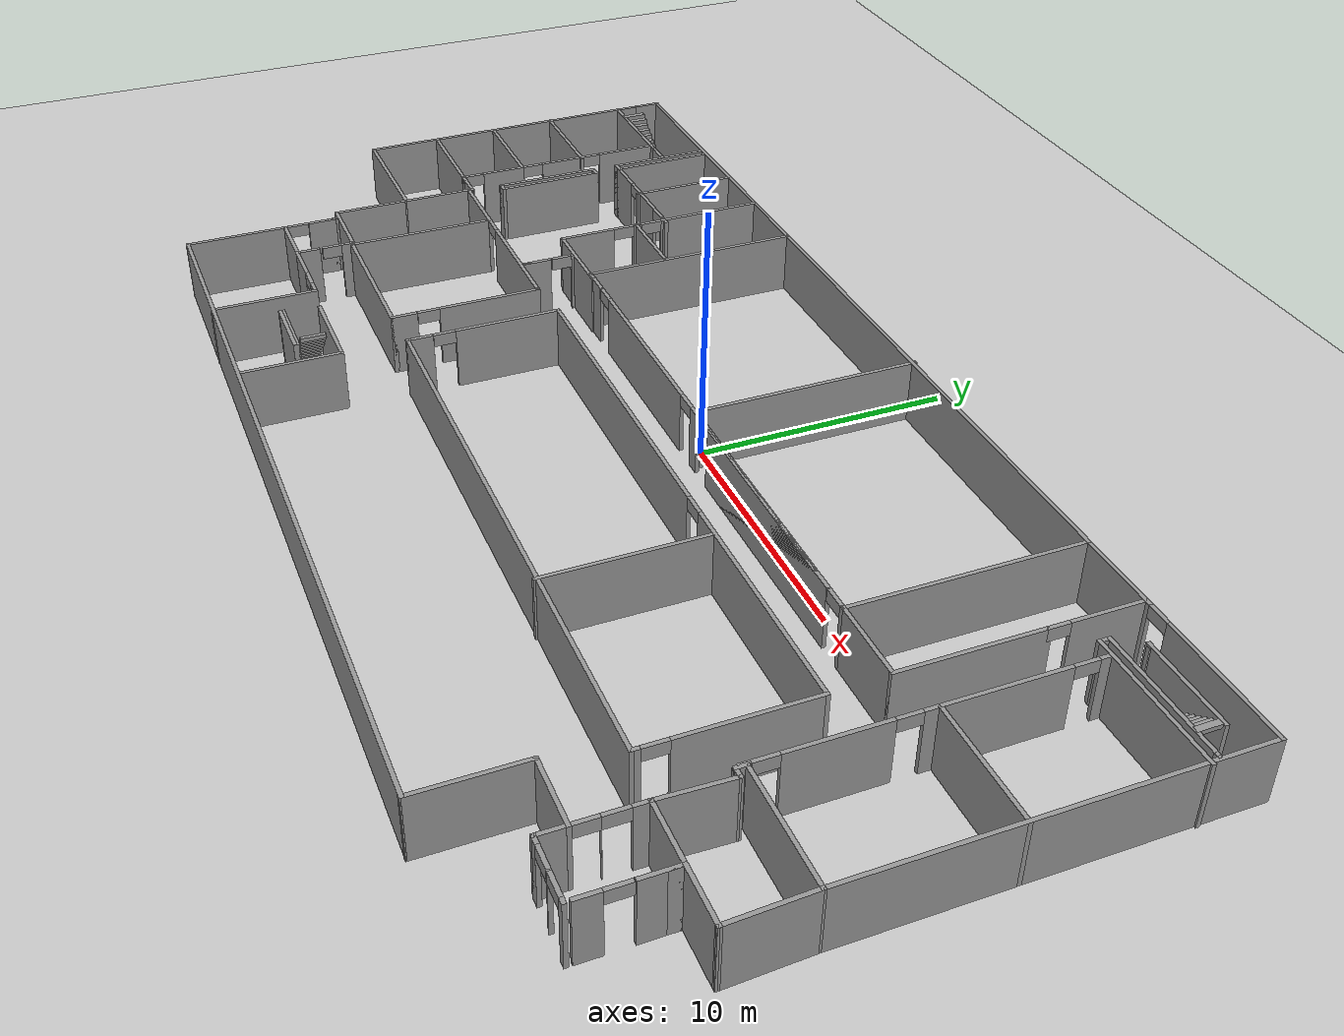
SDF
<sdf version='1.6'>
  <world name='default'>
    <light name='sun' type='directional'>
      <cast_shadows>1</cast_shadows>
      <pose frame=''>0 0 10 0 -0 0</pose>
      <diffuse>0.8 0.8 0.8 1</diffuse>
      <specular>0.1 0.1 0.1 1</specular>
      <attenuation>
        <range>1000</range>
        <constant>0.9</constant>
        <linear>0.01</linear>
        <quadratic>0.001</quadratic>
      </attenuation>
      <direction>-0.5 0.5 -1</direction>
    </light>
    <model name='ground_plane'>
      <static>1</static>
      <link name='link'>
        <collision name='collision'>
          <geometry>
            <plane>
              <normal>0 0 1</normal>
              <size>100 100</size>
            </plane>
          </geometry>
          <surface>
            <friction>
              <ode>
                <mu>100</mu>
                <mu2>50</mu2>
              </ode>
              <torsional>
                <ode/>
              </torsional>
            </friction>
            <contact>
              <ode/>
            </contact>
            <bounce/>
          </surface>
          <max_contacts>10</max_contacts>
        </collision>
        <visual name='visual'>
          <cast_shadows>0</cast_shadows>
          <geometry>
            <plane>
              <normal>0 0 1</normal>
              <size>100 100</size>
            </plane>
          </geometry>
          <material>
            <script>
              <uri>file://media/materials/scripts/gazebo.material</uri>
              <name>Gazebo/Grey</name>
            </script>
          </material>
        </visual>
        <self_collide>0</self_collide>
        <kinematic>0</kinematic>
        <gravity>1</gravity>
      </link>
    </model>
    <gravity>0 0 -9.8</gravity>
    <magnetic_field>6e-06 2.3e-05 -4.2e-05</magnetic_field>
    <atmosphere type='adiabatic'/>
    <physics name='default_physics' default='0' type='ode'>
      <max_step_size>0.001</max_step_size>
      <real_time_factor>1</real_time_factor>
      <real_time_update_rate>1000</real_time_update_rate>
    </physics>
    <scene>
      <ambient>0.4 0.4 0.4 1</ambient>
      <background>0.7 0.7 0.7 1</background>
      <shadows>1</shadows>
    </scene>
    <spherical_coordinates>
      <surface_model>EARTH_WGS84</surface_model>
      <latitude_deg>0</latitude_deg>
      <longitude_deg>0</longitude_deg>
      <elevation>0</elevation>
      <heading_deg>0</heading_deg>
    </spherical_coordinates>
    <model name='Devon1_test'>
      <pose frame=''>-1.37758 -3.56549 0 0 -0 0</pose>
      <link name='Stairs_5'>
        <visual name='Stairs_5_Visual_0'>
          <pose frame=''>-10.1985 -8.6433 0.083333 0 -0 1.5708</pose>
          <geometry>
            <box>
              <size>1 0.155676 0.166667</size>
            </box>
          </geometry>
          <material>
            <script>
              <uri>file://media/materials/scripts/gazebo.material</uri>
              <name>Gazebo/Grey</name>
            </script>
            <ambient>1 1 1 1</ambient>
          </material>
        </visual>
        <collision name='Stairs_5_Collision_0'>
          <geometry>
            <box>
              <size>1 0.155676 0.166667</size>
            </box>
          </geometry>
          <pose frame=''>-10.1985 -8.6433 0.083333 0 -0 1.5708</pose>
        </collision>
        <visual name='Stairs_5_Visual_1'>
          <pose frame=''>-10.0429 -8.6433 0.25 0 -0 1.5708</pose>
          <geometry>
            <box>
              <size>1 0.155676 0.166667</size>
            </box>
          </geometry>
          <material>
            <script>
              <uri>file://media/materials/scripts/gazebo.material</uri>
              <name>Gazebo/Grey</name>
            </script>
            <ambient>1 1 1 1</ambient>
          </material>
        </visual>
        <collision name='Stairs_5_Collision_1'>
          <geometry>
            <box>
              <size>1 0.155676 0.166667</size>
            </box>
          </geometry>
          <pose frame=''>-10.0429 -8.6433 0.25 0 -0 1.5708</pose>
        </collision>
        <visual name='Stairs_5_Visual_2'>
          <pose frame=''>-9.88718 -8.6433 0.416667 0 -0 1.5708</pose>
          <geometry>
            <box>
              <size>1 0.155676 0.166667</size>
            </box>
          </geometry>
          <material>
            <script>
              <uri>file://media/materials/scripts/gazebo.material</uri>
              <name>Gazebo/Grey</name>
            </script>
            <ambient>1 1 1 1</ambient>
          </material>
        </visual>
        <collision name='Stairs_5_Collision_2'>
          <geometry>
            <box>
              <size>1 0.155676 0.166667</size>
            </box>
          </geometry>
          <pose frame=''>-9.88718 -8.6433 0.416667 0 -0 1.5708</pose>
        </collision>
        <visual name='Stairs_5_Visual_3'>
          <pose frame=''>-9.7315 -8.6433 0.583333 0 -0 1.5708</pose>
          <geometry>
            <box>
              <size>1 0.155676 0.166667</size>
            </box>
          </geometry>
          <material>
            <script>
              <uri>file://media/materials/scripts/gazebo.material</uri>
              <name>Gazebo/Grey</name>
            </script>
            <ambient>1 1 1 1</ambient>
          </material>
        </visual>
        <collision name='Stairs_5_Collision_3'>
          <geometry>
            <box>
              <size>1 0.155676 0.166667</size>
            </box>
          </geometry>
          <pose frame=''>-9.7315 -8.6433 0.583333 0 -0 1.5708</pose>
        </collision>
        <visual name='Stairs_5_Visual_4'>
          <pose frame=''>-9.57583 -8.6433 0.75 0 -0 1.5708</pose>
          <geometry>
            <box>
              <size>1 0.155676 0.166667</size>
            </box>
          </geometry>
          <material>
            <script>
              <uri>file://media/materials/scripts/gazebo.material</uri>
              <name>Gazebo/Grey</name>
            </script>
            <ambient>1 1 1 1</ambient>
          </material>
        </visual>
        <collision name='Stairs_5_Collision_4'>
          <geometry>
            <box>
              <size>1 0.155676 0.166667</size>
            </box>
          </geometry>
          <pose frame=''>-9.57583 -8.6433 0.75 0 -0 1.5708</pose>
        </collision>
        <visual name='Stairs_5_Visual_5'>
          <pose frame=''>-9.42015 -8.6433 0.916667 0 -0 1.5708</pose>
          <geometry>
            <box>
              <size>1 0.155676 0.166667</size>
            </box>
          </geometry>
          <material>
            <script>
              <uri>file://media/materials/scripts/gazebo.material</uri>
              <name>Gazebo/Grey</name>
            </script>
            <ambient>1 1 1 1</ambient>
          </material>
        </visual>
        <collision name='Stairs_5_Collision_5'>
          <geometry>
            <box>
              <size>1 0.155676 0.166667</size>
            </box>
          </geometry>
          <pose frame=''>-9.42015 -8.6433 0.916667 0 -0 1.5708</pose>
        </collision>
        <visual name='Stairs_5_Visual_6'>
          <pose frame=''>-9.26447 -8.6433 1.08333 0 -0 1.5708</pose>
          <geometry>
            <box>
              <size>1 0.155676 0.166667</size>
            </box>
          </geometry>
          <material>
            <script>
              <uri>file://media/materials/scripts/gazebo.material</uri>
              <name>Gazebo/Grey</name>
            </script>
            <ambient>1 1 1 1</ambient>
          </material>
        </visual>
        <collision name='Stairs_5_Collision_6'>
          <geometry>
            <box>
              <size>1 0.155676 0.166667</size>
            </box>
          </geometry>
          <pose frame=''>-9.26447 -8.6433 1.08333 0 -0 1.5708</pose>
        </collision>
        <visual name='Stairs_5_Visual_7'>
          <pose frame=''>-9.1088 -8.6433 1.25 0 -0 1.5708</pose>
          <geometry>
            <box>
              <size>1 0.155676 0.166667</size>
            </box>
          </geometry>
          <material>
            <script>
              <uri>file://media/materials/scripts/gazebo.material</uri>
              <name>Gazebo/Grey</name>
            </script>
            <ambient>1 1 1 1</ambient>
          </material>
        </visual>
        <collision name='Stairs_5_Collision_7'>
          <geometry>
            <box>
              <size>1 0.155676 0.166667</size>
            </box>
          </geometry>
          <pose frame=''>-9.1088 -8.6433 1.25 0 -0 1.5708</pose>
        </collision>
        <visual name='Stairs_5_Visual_8'>
          <pose frame=''>-8.95312 -8.6433 1.41667 0 -0 1.5708</pose>
          <geometry>
            <box>
              <size>1 0.155676 0.166667</size>
            </box>
          </geometry>
          <material>
            <script>
              <uri>file://media/materials/scripts/gazebo.material</uri>
              <name>Gazebo/Grey</name>
            </script>
            <ambient>1 1 1 1</ambient>
          </material>
        </visual>
        <collision name='Stairs_5_Collision_8'>
          <geometry>
            <box>
              <size>1 0.155676 0.166667</size>
            </box>
          </geometry>
          <pose frame=''>-8.95312 -8.6433 1.41667 0 -0 1.5708</pose>
        </collision>
        <visual name='Stairs_5_Visual_9'>
          <pose frame=''>-8.79744 -8.6433 1.58333 0 -0 1.5708</pose>
          <geometry>
            <box>
              <size>1 0.155676 0.166667</size>
            </box>
          </geometry>
          <material>
            <script>
              <uri>file://media/materials/scripts/gazebo.material</uri>
              <name>Gazebo/Grey</name>
            </script>
            <ambient>1 1 1 1</ambient>
          </material>
        </visual>
        <collision name='Stairs_5_Collision_9'>
          <geometry>
            <box>
              <size>1 0.155676 0.166667</size>
            </box>
          </geometry>
          <pose frame=''>-8.79744 -8.6433 1.58333 0 -0 1.5708</pose>
        </collision>
        <visual name='Stairs_5_Visual_10'>
          <pose frame=''>-8.64177 -8.6433 1.75 0 -0 1.5708</pose>
          <geometry>
            <box>
              <size>1 0.155676 0.166667</size>
            </box>
          </geometry>
          <material>
            <script>
              <uri>file://media/materials/scripts/gazebo.material</uri>
              <name>Gazebo/Grey</name>
            </script>
            <ambient>1 1 1 1</ambient>
          </material>
        </visual>
        <collision name='Stairs_5_Collision_10'>
          <geometry>
            <box>
              <size>1 0.155676 0.166667</size>
            </box>
          </geometry>
          <pose frame=''>-8.64177 -8.6433 1.75 0 -0 1.5708</pose>
        </collision>
        <visual name='Stairs_5_Visual_11'>
          <pose frame=''>-8.48609 -8.6433 1.91667 0 -0 1.5708</pose>
          <geometry>
            <box>
              <size>1 0.155676 0.166667</size>
            </box>
          </geometry>
          <material>
            <script>
              <uri>file://media/materials/scripts/gazebo.material</uri>
              <name>Gazebo/Grey</name>
            </script>
            <ambient>1 1 1 1</ambient>
          </material>
        </visual>
        <collision name='Stairs_5_Collision_11'>
          <geometry>
            <box>
              <size>1 0.155676 0.166667</size>
            </box>
          </geometry>
          <pose frame=''>-8.48609 -8.6433 1.91667 0 -0 1.5708</pose>
        </collision>
        <visual name='Stairs_5_Visual_12'>
          <pose frame=''>-8.33042 -8.6433 2.08333 0 -0 1.5708</pose>
          <geometry>
            <box>
              <size>1 0.155676 0.166667</size>
            </box>
          </geometry>
          <material>
            <script>
              <uri>file://media/materials/scripts/gazebo.material</uri>
              <name>Gazebo/Grey</name>
            </script>
            <ambient>1 1 1 1</ambient>
          </material>
        </visual>
        <collision name='Stairs_5_Collision_12'>
          <geometry>
            <box>
              <size>1 0.155676 0.166667</size>
            </box>
          </geometry>
          <pose frame=''>-8.33042 -8.6433 2.08333 0 -0 1.5708</pose>
        </collision>
        <visual name='Stairs_5_Visual_13'>
          <pose frame=''>-8.17474 -8.6433 2.25 0 -0 1.5708</pose>
          <geometry>
            <box>
              <size>1 0.155676 0.166667</size>
            </box>
          </geometry>
          <material>
            <script>
              <uri>file://media/materials/scripts/gazebo.material</uri>
              <name>Gazebo/Grey</name>
            </script>
            <ambient>1 1 1 1</ambient>
          </material>
        </visual>
        <collision name='Stairs_5_Collision_13'>
          <geometry>
            <box>
              <size>1 0.155676 0.166667</size>
            </box>
          </geometry>
          <pose frame=''>-8.17474 -8.6433 2.25 0 -0 1.5708</pose>
        </collision>
        <visual name='Stairs_5_Visual_14'>
          <pose frame=''>-8.01906 -8.6433 2.41667 0 -0 1.5708</pose>
          <geometry>
            <box>
              <size>1 0.155676 0.166667</size>
            </box>
          </geometry>
          <material>
            <script>
              <uri>file://media/materials/scripts/gazebo.material</uri>
              <name>Gazebo/Grey</name>
            </script>
            <ambient>1 1 1 1</ambient>
          </material>
        </visual>
        <collision name='Stairs_5_Collision_14'>
          <geometry>
            <box>
              <size>1 0.155676 0.166667</size>
            </box>
          </geometry>
          <pose frame=''>-8.01906 -8.6433 2.41667 0 -0 1.5708</pose>
        </collision>
      </link>
      <link name='Stairs_6'>
        <visual name='Stairs_6_Visual_0'>
          <pose frame=''>-18.9091 10.232 0.083333 0 -0 -1.5708</pose>
          <geometry>
            <box>
              <size>1 0.233333 0.166667</size>
            </box>
          </geometry>
          <material>
            <script>
              <uri>file://media/materials/scripts/gazebo.material</uri>
              <name>Gazebo/Grey</name>
            </script>
            <ambient>1 1 1 1</ambient>
          </material>
        </visual>
        <collision name='Stairs_6_Collision_0'>
          <geometry>
            <box>
              <size>1 0.233333 0.166667</size>
            </box>
          </geometry>
          <pose frame=''>-18.9091 10.232 0.083333 0 -0 -1.5708</pose>
        </collision>
        <visual name='Stairs_6_Visual_1'>
          <pose frame=''>-19.1424 10.232 0.25 0 -0 -1.5708</pose>
          <geometry>
            <box>
              <size>1 0.233333 0.166667</size>
            </box>
          </geometry>
          <material>
            <script>
              <uri>file://media/materials/scripts/gazebo.material</uri>
              <name>Gazebo/Grey</name>
            </script>
            <ambient>1 1 1 1</ambient>
          </material>
        </visual>
        <collision name='Stairs_6_Collision_1'>
          <geometry>
            <box>
              <size>1 0.233333 0.166667</size>
            </box>
          </geometry>
          <pose frame=''>-19.1424 10.232 0.25 0 -0 -1.5708</pose>
        </collision>
        <visual name='Stairs_6_Visual_2'>
          <pose frame=''>-19.3758 10.232 0.416667 0 -0 -1.5708</pose>
          <geometry>
            <box>
              <size>1 0.233333 0.166667</size>
            </box>
          </geometry>
          <material>
            <script>
              <uri>file://media/materials/scripts/gazebo.material</uri>
              <name>Gazebo/Grey</name>
            </script>
            <ambient>1 1 1 1</ambient>
          </material>
        </visual>
        <collision name='Stairs_6_Collision_2'>
          <geometry>
            <box>
              <size>1 0.233333 0.166667</size>
            </box>
          </geometry>
          <pose frame=''>-19.3758 10.232 0.416667 0 -0 -1.5708</pose>
        </collision>
        <visual name='Stairs_6_Visual_3'>
          <pose frame=''>-19.6091 10.232 0.583333 0 -0 -1.5708</pose>
          <geometry>
            <box>
              <size>1 0.233333 0.166667</size>
            </box>
          </geometry>
          <material>
            <script>
              <uri>file://media/materials/scripts/gazebo.material</uri>
              <name>Gazebo/Grey</name>
            </script>
            <ambient>1 1 1 1</ambient>
          </material>
        </visual>
        <collision name='Stairs_6_Collision_3'>
          <geometry>
            <box>
              <size>1 0.233333 0.166667</size>
            </box>
          </geometry>
          <pose frame=''>-19.6091 10.232 0.583333 0 -0 -1.5708</pose>
        </collision>
        <visual name='Stairs_6_Visual_4'>
          <pose frame=''>-19.8424 10.232 0.75 0 -0 -1.5708</pose>
          <geometry>
            <box>
              <size>1 0.233333 0.166667</size>
            </box>
          </geometry>
          <material>
            <script>
              <uri>file://media/materials/scripts/gazebo.material</uri>
              <name>Gazebo/Grey</name>
            </script>
            <ambient>1 1 1 1</ambient>
          </material>
        </visual>
        <collision name='Stairs_6_Collision_4'>
          <geometry>
            <box>
              <size>1 0.233333 0.166667</size>
            </box>
          </geometry>
          <pose frame=''>-19.8424 10.232 0.75 0 -0 -1.5708</pose>
        </collision>
        <visual name='Stairs_6_Visual_5'>
          <pose frame=''>-20.0757 10.232 0.916667 0 -0 -1.5708</pose>
          <geometry>
            <box>
              <size>1 0.233333 0.166667</size>
            </box>
          </geometry>
          <material>
            <script>
              <uri>file://media/materials/scripts/gazebo.material</uri>
              <name>Gazebo/Grey</name>
            </script>
            <ambient>1 1 1 1</ambient>
          </material>
        </visual>
        <collision name='Stairs_6_Collision_5'>
          <geometry>
            <box>
              <size>1 0.233333 0.166667</size>
            </box>
          </geometry>
          <pose frame=''>-20.0757 10.232 0.916667 0 -0 -1.5708</pose>
        </collision>
        <visual name='Stairs_6_Visual_6'>
          <pose frame=''>-20.3091 10.232 1.08333 0 -0 -1.5708</pose>
          <geometry>
            <box>
              <size>1 0.233333 0.166667</size>
            </box>
          </geometry>
          <material>
            <script>
              <uri>file://media/materials/scripts/gazebo.material</uri>
              <name>Gazebo/Grey</name>
            </script>
            <ambient>1 1 1 1</ambient>
          </material>
        </visual>
        <collision name='Stairs_6_Collision_6'>
          <geometry>
            <box>
              <size>1 0.233333 0.166667</size>
            </box>
          </geometry>
          <pose frame=''>-20.3091 10.232 1.08333 0 -0 -1.5708</pose>
        </collision>
        <visual name='Stairs_6_Visual_7'>
          <pose frame=''>-20.5424 10.232 1.25 0 -0 -1.5708</pose>
          <geometry>
            <box>
              <size>1 0.233333 0.166667</size>
            </box>
          </geometry>
          <material>
            <script>
              <uri>file://media/materials/scripts/gazebo.material</uri>
              <name>Gazebo/Grey</name>
            </script>
            <ambient>1 1 1 1</ambient>
          </material>
        </visual>
        <collision name='Stairs_6_Collision_7'>
          <geometry>
            <box>
              <size>1 0.233333 0.166667</size>
            </box>
          </geometry>
          <pose frame=''>-20.5424 10.232 1.25 0 -0 -1.5708</pose>
        </collision>
        <visual name='Stairs_6_Visual_8'>
          <pose frame=''>-20.7757 10.232 1.41667 0 -0 -1.5708</pose>
          <geometry>
            <box>
              <size>1 0.233333 0.166667</size>
            </box>
          </geometry>
          <material>
            <script>
              <uri>file://media/materials/scripts/gazebo.material</uri>
              <name>Gazebo/Grey</name>
            </script>
            <ambient>1 1 1 1</ambient>
          </material>
        </visual>
        <collision name='Stairs_6_Collision_8'>
          <geometry>
            <box>
              <size>1 0.233333 0.166667</size>
            </box>
          </geometry>
          <pose frame=''>-20.7757 10.232 1.41667 0 -0 -1.5708</pose>
        </collision>
        <visual name='Stairs_6_Visual_9'>
          <pose frame=''>-21.0091 10.232 1.58333 0 -0 -1.5708</pose>
          <geometry>
            <box>
              <size>1 0.233333 0.166667</size>
            </box>
          </geometry>
          <material>
            <script>
              <uri>file://media/materials/scripts/gazebo.material</uri>
              <name>Gazebo/Grey</name>
            </script>
            <ambient>1 1 1 1</ambient>
          </material>
        </visual>
        <collision name='Stairs_6_Collision_9'>
          <geometry>
            <box>
              <size>1 0.233333 0.166667</size>
            </box>
          </geometry>
          <pose frame=''>-21.0091 10.232 1.58333 0 -0 -1.5708</pose>
        </collision>
        <visual name='Stairs_6_Visual_10'>
          <pose frame=''>-21.2424 10.232 1.75 0 -0 -1.5708</pose>
          <geometry>
            <box>
              <size>1 0.233333 0.166667</size>
            </box>
          </geometry>
          <material>
            <script>
              <uri>file://media/materials/scripts/gazebo.material</uri>
              <name>Gazebo/Grey</name>
            </script>
            <ambient>1 1 1 1</ambient>
          </material>
        </visual>
        <collision name='Stairs_6_Collision_10'>
          <geometry>
            <box>
              <size>1 0.233333 0.166667</size>
            </box>
          </geometry>
          <pose frame=''>-21.2424 10.232 1.75 0 -0 -1.5708</pose>
        </collision>
        <visual name='Stairs_6_Visual_11'>
          <pose frame=''>-21.4758 10.232 1.91667 0 -0 -1.5708</pose>
          <geometry>
            <box>
              <size>1 0.233333 0.166667</size>
            </box>
          </geometry>
          <material>
            <script>
              <uri>file://media/materials/scripts/gazebo.material</uri>
              <name>Gazebo/Grey</name>
            </script>
            <ambient>1 1 1 1</ambient>
          </material>
        </visual>
        <collision name='Stairs_6_Collision_11'>
          <geometry>
            <box>
              <size>1 0.233333 0.166667</size>
            </box>
          </geometry>
          <pose frame=''>-21.4758 10.232 1.91667 0 -0 -1.5708</pose>
        </collision>
        <visual name='Stairs_6_Visual_12'>
          <pose frame=''>-21.7091 10.232 2.08333 0 -0 -1.5708</pose>
          <geometry>
            <box>
              <size>1 0.233333 0.166667</size>
            </box>
          </geometry>
          <material>
            <script>
              <uri>file://media/materials/scripts/gazebo.material</uri>
              <name>Gazebo/Grey</name>
            </script>
            <ambient>1 1 1 1</ambient>
          </material>
        </visual>
        <collision name='Stairs_6_Collision_12'>
          <geometry>
            <box>
              <size>1 0.233333 0.166667</size>
            </box>
          </geometry>
          <pose frame=''>-21.7091 10.232 2.08333 0 -0 -1.5708</pose>
        </collision>
        <visual name='Stairs_6_Visual_13'>
          <pose frame=''>-21.9424 10.232 2.25 0 -0 -1.5708</pose>
          <geometry>
            <box>
              <size>1 0.233333 0.166667</size>
            </box>
          </geometry>
          <material>
            <script>
              <uri>file://media/materials/scripts/gazebo.material</uri>
              <name>Gazebo/Grey</name>
            </script>
            <ambient>1 1 1 1</ambient>
          </material>
        </visual>
        <collision name='Stairs_6_Collision_13'>
          <geometry>
            <box>
              <size>1 0.233333 0.166667</size>
            </box>
          </geometry>
          <pose frame=''>-21.9424 10.232 2.25 0 -0 -1.5708</pose>
        </collision>
        <visual name='Stairs_6_Visual_14'>
          <pose frame=''>-22.1757 10.232 2.41667 0 -0 -1.5708</pose>
          <geometry>
            <box>
              <size>1 0.233333 0.166667</size>
            </box>
          </geometry>
          <material>
            <script>
              <uri>file://media/materials/scripts/gazebo.material</uri>
              <name>Gazebo/Grey</name>
            </script>
            <ambient>1 1 1 1</ambient>
          </material>
        </visual>
        <collision name='Stairs_6_Collision_14'>
          <geometry>
            <box>
              <size>1 0.233333 0.166667</size>
            </box>
          </geometry>
          <pose frame=''>-22.1757 10.232 2.41667 0 -0 -1.5708</pose>
        </collision>
      </link>
      <link name='Stairs_8'>
        <visual name='Stairs_8_Visual_0'>
          <pose frame=''>18.5359 10.1599 0.083333 0 -0 1.5708</pose>
          <geometry>
            <box>
              <size>0.910609 0.233333 0.166667</size>
            </box>
          </geometry>
          <material>
            <script>
              <uri>file://media/materials/scripts/gazebo.material</uri>
              <name>Gazebo/Grey</name>
            </script>
            <ambient>1 1 1 1</ambient>
          </material>
        </visual>
        <collision name='Stairs_8_Collision_0'>
          <geometry>
            <box>
              <size>0.910609 0.233333 0.166667</size>
            </box>
          </geometry>
          <pose frame=''>18.5359 10.1599 0.083333 0 -0 1.5708</pose>
        </collision>
        <visual name='Stairs_8_Visual_1'>
          <pose frame=''>18.7693 10.1599 0.25 0 -0 1.5708</pose>
          <geometry>
            <box>
              <size>0.910609 0.233333 0.166667</size>
            </box>
          </geometry>
          <material>
            <script>
              <uri>file://media/materials/scripts/gazebo.material</uri>
              <name>Gazebo/Grey</name>
            </script>
            <ambient>1 1 1 1</ambient>
          </material>
        </visual>
        <collision name='Stairs_8_Collision_1'>
          <geometry>
            <box>
              <size>0.910609 0.233333 0.166667</size>
            </box>
          </geometry>
          <pose frame=''>18.7693 10.1599 0.25 0 -0 1.5708</pose>
        </collision>
        <visual name='Stairs_8_Visual_2'>
          <pose frame=''>19.0026 10.1599 0.416667 0 -0 1.5708</pose>
          <geometry>
            <box>
              <size>0.910609 0.233333 0.166667</size>
            </box>
          </geometry>
          <material>
            <script>
              <uri>file://media/materials/scripts/gazebo.material</uri>
              <name>Gazebo/Grey</name>
            </script>
            <ambient>1 1 1 1</ambient>
          </material>
        </visual>
        <collision name='Stairs_8_Collision_2'>
          <geometry>
            <box>
              <size>0.910609 0.233333 0.166667</size>
            </box>
          </geometry>
          <pose frame=''>19.0026 10.1599 0.416667 0 -0 1.5708</pose>
        </collision>
        <visual name='Stairs_8_Visual_3'>
          <pose frame=''>19.2359 10.1599 0.583333 0 -0 1.5708</pose>
          <geometry>
            <box>
              <size>0.910609 0.233333 0.166667</size>
            </box>
          </geometry>
          <material>
            <script>
              <uri>file://media/materials/scripts/gazebo.material</uri>
              <name>Gazebo/Grey</name>
            </script>
            <ambient>1 1 1 1</ambient>
          </material>
        </visual>
        <collision name='Stairs_8_Collision_3'>
          <geometry>
            <box>
              <size>0.910609 0.233333 0.166667</size>
            </box>
          </geometry>
          <pose frame=''>19.2359 10.1599 0.583333 0 -0 1.5708</pose>
        </collision>
        <visual name='Stairs_8_Visual_4'>
          <pose frame=''>19.4693 10.1599 0.75 0 -0 1.5708</pose>
          <geometry>
            <box>
              <size>0.910609 0.233333 0.166667</size>
            </box>
          </geometry>
          <material>
            <script>
              <uri>file://media/materials/scripts/gazebo.material</uri>
              <name>Gazebo/Grey</name>
            </script>
            <ambient>1 1 1 1</ambient>
          </material>
        </visual>
        <collision name='Stairs_8_Collision_4'>
          <geometry>
            <box>
              <size>0.910609 0.233333 0.166667</size>
            </box>
          </geometry>
          <pose frame=''>19.4693 10.1599 0.75 0 -0 1.5708</pose>
        </collision>
        <visual name='Stairs_8_Visual_5'>
          <pose frame=''>19.7026 10.1599 0.916667 0 -0 1.5708</pose>
          <geometry>
            <box>
              <size>0.910609 0.233333 0.166667</size>
            </box>
          </geometry>
          <material>
            <script>
              <uri>file://media/materials/scripts/gazebo.material</uri>
              <name>Gazebo/Grey</name>
            </script>
            <ambient>1 1 1 1</ambient>
          </material>
        </visual>
        <collision name='Stairs_8_Collision_5'>
          <geometry>
            <box>
              <size>0.910609 0.233333 0.166667</size>
            </box>
          </geometry>
          <pose frame=''>19.7026 10.1599 0.916667 0 -0 1.5708</pose>
        </collision>
        <visual name='Stairs_8_Visual_6'>
          <pose frame=''>19.9359 10.1599 1.08333 0 -0 1.5708</pose>
          <geometry>
            <box>
              <size>0.910609 0.233333 0.166667</size>
            </box>
          </geometry>
          <material>
            <script>
              <uri>file://media/materials/scripts/gazebo.material</uri>
              <name>Gazebo/Grey</name>
            </script>
            <ambient>1 1 1 1</ambient>
          </material>
        </visual>
        <collision name='Stairs_8_Collision_6'>
          <geometry>
            <box>
              <size>0.910609 0.233333 0.166667</size>
            </box>
          </geometry>
          <pose frame=''>19.9359 10.1599 1.08333 0 -0 1.5708</pose>
        </collision>
        <visual name='Stairs_8_Visual_7'>
          <pose frame=''>20.1693 10.1599 1.25 0 -0 1.5708</pose>
          <geometry>
            <box>
              <size>0.910609 0.233333 0.166667</size>
            </box>
          </geometry>
          <material>
            <script>
              <uri>file://media/materials/scripts/gazebo.material</uri>
              <name>Gazebo/Grey</name>
            </script>
            <ambient>1 1 1 1</ambient>
          </material>
        </visual>
        <collision name='Stairs_8_Collision_7'>
          <geometry>
            <box>
              <size>0.910609 0.233333 0.166667</size>
            </box>
          </geometry>
          <pose frame=''>20.1693 10.1599 1.25 0 -0 1.5708</pose>
        </collision>
        <visual name='Stairs_8_Visual_8'>
          <pose frame=''>20.4026 10.1599 1.41667 0 -0 1.5708</pose>
          <geometry>
            <box>
              <size>0.910609 0.233333 0.166667</size>
            </box>
          </geometry>
          <material>
            <script>
              <uri>file://media/materials/scripts/gazebo.material</uri>
              <name>Gazebo/Grey</name>
            </script>
            <ambient>1 1 1 1</ambient>
          </material>
        </visual>
        <collision name='Stairs_8_Collision_8'>
          <geometry>
            <box>
              <size>0.910609 0.233333 0.166667</size>
            </box>
          </geometry>
          <pose frame=''>20.4026 10.1599 1.41667 0 -0 1.5708</pose>
        </collision>
        <visual name='Stairs_8_Visual_9'>
          <pose frame=''>20.6359 10.1599 1.58333 0 -0 1.5708</pose>
          <geometry>
            <box>
              <size>0.910609 0.233333 0.166667</size>
            </box>
          </geometry>
          <material>
            <script>
              <uri>file://media/materials/scripts/gazebo.material</uri>
              <name>Gazebo/Grey</name>
            </script>
            <ambient>1 1 1 1</ambient>
          </material>
        </visual>
        <collision name='Stairs_8_Collision_9'>
          <geometry>
            <box>
              <size>0.910609 0.233333 0.166667</size>
            </box>
          </geometry>
          <pose frame=''>20.6359 10.1599 1.58333 0 -0 1.5708</pose>
        </collision>
        <visual name='Stairs_8_Visual_10'>
          <pose frame=''>20.8693 10.1599 1.75 0 -0 1.5708</pose>
          <geometry>
            <box>
              <size>0.910609 0.233333 0.166667</size>
            </box>
          </geometry>
          <material>
            <script>
              <uri>file://media/materials/scripts/gazebo.material</uri>
              <name>Gazebo/Grey</name>
            </script>
            <ambient>1 1 1 1</ambient>
          </material>
        </visual>
        <collision name='Stairs_8_Collision_10'>
          <geometry>
            <box>
              <size>0.910609 0.233333 0.166667</size>
            </box>
          </geometry>
          <pose frame=''>20.8693 10.1599 1.75 0 -0 1.5708</pose>
        </collision>
        <visual name='Stairs_8_Visual_11'>
          <pose frame=''>21.1026 10.1599 1.91667 0 -0 1.5708</pose>
          <geometry>
            <box>
              <size>0.910609 0.233333 0.166667</size>
            </box>
          </geometry>
          <material>
            <script>
              <uri>file://media/materials/scripts/gazebo.material</uri>
              <name>Gazebo/Grey</name>
            </script>
            <ambient>1 1 1 1</ambient>
          </material>
        </visual>
        <collision name='Stairs_8_Collision_11'>
          <geometry>
            <box>
              <size>0.910609 0.233333 0.166667</size>
            </box>
          </geometry>
          <pose frame=''>21.1026 10.1599 1.91667 0 -0 1.5708</pose>
        </collision>
        <visual name='Stairs_8_Visual_12'>
          <pose frame=''>21.3359 10.1599 2.08333 0 -0 1.5708</pose>
          <geometry>
            <box>
              <size>0.910609 0.233333 0.166667</size>
            </box>
          </geometry>
          <material>
            <script>
              <uri>file://media/materials/scripts/gazebo.material</uri>
              <name>Gazebo/Grey</name>
            </script>
            <ambient>1 1 1 1</ambient>
          </material>
        </visual>
        <collision name='Stairs_8_Collision_12'>
          <geometry>
            <box>
              <size>0.910609 0.233333 0.166667</size>
            </box>
          </geometry>
          <pose frame=''>21.3359 10.1599 2.08333 0 -0 1.5708</pose>
        </collision>
        <visual name='Stairs_8_Visual_13'>
          <pose frame=''>21.5693 10.1599 2.25 0 -0 1.5708</pose>
          <geometry>
            <box>
              <size>0.910609 0.233333 0.166667</size>
            </box>
          </geometry>
          <material>
            <script>
              <uri>file://media/materials/scripts/gazebo.material</uri>
              <name>Gazebo/Grey</name>
            </script>
            <ambient>1 1 1 1</ambient>
          </material>
        </visual>
        <collision name='Stairs_8_Collision_13'>
          <geometry>
            <box>
              <size>0.910609 0.233333 0.166667</size>
            </box>
          </geometry>
          <pose frame=''>21.5693 10.1599 2.25 0 -0 1.5708</pose>
        </collision>
        <visual name='Stairs_8_Visual_14'>
          <pose frame=''>21.8026 10.1599 2.41667 0 -0 1.5708</pose>
          <geometry>
            <box>
              <size>0.910609 0.233333 0.166667</size>
            </box>
          </geometry>
          <material>
            <script>
              <uri>file://media/materials/scripts/gazebo.material</uri>
              <name>Gazebo/Grey</name>
            </script>
            <ambient>1 1 1 1</ambient>
          </material>
        </visual>
        <collision name='Stairs_8_Collision_14'>
          <geometry>
            <box>
              <size>0.910609 0.233333 0.166667</size>
            </box>
          </geometry>
          <pose frame=''>21.8026 10.1599 2.41667 0 -0 1.5708</pose>
        </collision>
      </link>
      <link name='Wall_0'>
        <collision name='Wall_0_Collision'>
          <geometry>
            <box>
              <size>9 0.15 2.5</size>
            </box>
          </geometry>
          <pose frame=''>0 0 1.25 0 -0 0</pose>
        </collision>
        <visual name='Wall_0_Visual'>
          <pose frame=''>0 0 1.25 0 -0 0</pose>
          <geometry>
            <box>
              <size>9 0.15 2.5</size>
            </box>
          </geometry>
          <material>
            <script>
              <uri>file://media/materials/scripts/gazebo.material</uri>
              <name>Gazebo/Grey</name>
            </script>
            <ambient>1 1 1 1</ambient>
          </material>
        </visual>
        <pose frame=''>13.5343 7.35639 0 0 0 -1.5708</pose>
      </link>
      <link name='Wall_1'>
        <collision name='Wall_1_Collision'>
          <geometry>
            <box>
              <size>3.25 0.15 2.5</size>
            </box>
          </geometry>
          <pose frame=''>0 0 1.25 0 -0 0</pose>
        </collision>
        <visual name='Wall_1_Visual'>
          <pose frame=''>0 0 1.25 0 -0 0</pose>
          <geometry>
            <box>
              <size>3.25 0.15 2.5</size>
            </box>
          </geometry>
          <material>
            <script>
              <uri>file://media/materials/scripts/gazebo.material</uri>
              <name>Gazebo/Grey</name>
            </script>
            <ambient>1 1 1 1</ambient>
          </material>
        </visual>
        <pose frame=''>15.0843 2.93139 0 0 -0 0</pose>
      </link>
      <link name='Wall_103'>
        <collision name='Wall_103_Collision'>
          <geometry>
            <box>
              <size>2.25 0.15 2.5</size>
            </box>
          </geometry>
          <pose frame=''>0 0 1.25 0 -0 0</pose>
        </collision>
        <visual name='Wall_103_Visual'>
          <pose frame=''>0 0 1.25 0 -0 0</pose>
          <geometry>
            <box>
              <size>2.25 0.15 2.5</size>
            </box>
          </geometry>
          <material>
            <script>
              <uri>file://media/materials/scripts/gazebo.material</uri>
              <name>Gazebo/Grey</name>
            </script>
            <ambient>1 1 1 1</ambient>
          </material>
        </visual>
        <pose frame=''>22.0343 -5.51861 0 0 -0 0</pose>
      </link>
      <link name='Wall_104'>
        <collision name='Wall_104_Collision'>
          <geometry>
            <box>
              <size>3.10169 0.15 2.5</size>
            </box>
          </geometry>
          <pose frame=''>0 0 1.25 0 -0 0</pose>
        </collision>
        <visual name='Wall_104_Visual'>
          <pose frame=''>0 0 1.25 0 -0 0</pose>
          <geometry>
            <box>
              <size>3.10169 0.15 2.5</size>
            </box>
          </geometry>
          <material>
            <script>
              <uri>file://media/materials/scripts/gazebo.material</uri>
              <name>Gazebo/Grey</name>
            </script>
            <ambient>1 1 1 1</ambient>
          </material>
        </visual>
        <pose frame=''>23.0343 -4.04361 0 0 -0 1.60468</pose>
      </link>
      <link name='Wall_106'>
        <collision name='Wall_106_Collision'>
          <geometry>
            <box>
              <size>0.5 0.15 2.5</size>
            </box>
          </geometry>
          <pose frame=''>0 0 1.25 0 -0 0</pose>
        </collision>
        <visual name='Wall_106_Visual'>
          <pose frame=''>0 0 1.25 0 -0 0</pose>
          <geometry>
            <box>
              <size>0.5 0.15 2.5</size>
            </box>
          </geometry>
          <material>
            <script>
              <uri>file://media/materials/scripts/gazebo.material</uri>
              <name>Gazebo/Grey</name>
            </script>
            <ambient>1 1 1 1</ambient>
          </material>
        </visual>
        <pose frame=''>18.3843 -2.74361 0 0 0 -1.5708</pose>
      </link>
      <link name='Wall_107'>
        <collision name='Wall_107_Collision'>
          <geometry>
            <box>
              <size>0.5 0.15 2.5</size>
            </box>
          </geometry>
          <pose frame=''>0 0 1.25 0 -0 0</pose>
        </collision>
        <visual name='Wall_107_Visual'>
          <pose frame=''>0 0 1.25 0 -0 0</pose>
          <geometry>
            <box>
              <size>0.5 0.15 2.5</size>
            </box>
          </geometry>
          <material>
            <script>
              <uri>file://media/materials/scripts/gazebo.material</uri>
              <name>Gazebo/Grey</name>
            </script>
            <ambient>1 1 1 1</ambient>
          </material>
        </visual>
        <pose frame=''>18.5593 -2.91861 0 0 -0 0</pose>
      </link>
      <link name='Wall_108'>
        <collision name='Wall_108_Collision'>
          <geometry>
            <box>
              <size>2.75192 0.15 2.5</size>
            </box>
          </geometry>
          <pose frame=''>0 0 1.25 0 -0 0</pose>
        </collision>
        <visual name='Wall_108_Visual'>
          <pose frame=''>0 0 1.25 0 -0 0</pose>
          <geometry>
            <box>
              <size>2.75192 0.15 2.5</size>
            </box>
          </geometry>
          <material>
            <script>
              <uri>file://media/materials/scripts/gazebo.material</uri>
              <name>Gazebo/Grey</name>
            </script>
            <ambient>1 1 1 1</ambient>
          </material>
        </visual>
        <pose frame=''>18.6843 -4.21861 0 0 0 -1.60924</pose>
      </link>
      <link name='Wall_11'>
        <pose frame=''>19.8093 11.7814 0 0 -0 0</pose>
        <visual name='Wall_11_Visual_0'>
          <pose frame=''>-3.09331 0 1.25 0 -0 0</pose>
          <geometry>
            <box>
              <size>0.31338 0.15 2.5</size>
            </box>
          </geometry>
          <material>
            <script>
              <uri>file://media/materials/scripts/gazebo.material</uri>
              <name>Gazebo/Grey</name>
            </script>
            <ambient>1 1 1 1</ambient>
          </material>
        </visual>
        <collision name='Wall_11_Collision_0'>
          <geometry>
            <box>
              <size>0.31338 0.15 2.5</size>
            </box>
          </geometry>
          <pose frame=''>-3.09331 0 1.25 0 -0 0</pose>
        </collision>
        <visual name='Wall_11_Visual_1'>
          <pose frame=''>0.60669 0 1.25 0 -0 0</pose>
          <geometry>
            <box>
              <size>5.28662 0.15 2.5</size>
            </box>
          </geometry>
          <material>
            <script>
              <uri>file://media/materials/scripts/gazebo.material</uri>
              <name>Gazebo/Grey</name>
            </script>
            <ambient>1 1 1 1</ambient>
          </material>
        </visual>
        <collision name='Wall_11_Collision_1'>
          <geometry>
            <box>
              <size>5.28662 0.15 2.5</size>
            </box>
          </geometry>
          <pose frame=''>0.60669 0 1.25 0 -0 0</pose>
        </collision>
        <visual name='Wall_11_Visual_2'>
          <pose frame=''>-2.48662 0 2.25 0 -0 0</pose>
          <geometry>
            <box>
              <size>0.9 0.15 0.5</size>
            </box>
          </geometry>
          <material>
            <script>
              <uri>file://media/materials/scripts/gazebo.material</uri>
              <name>Gazebo/Grey</name>
            </script>
            <ambient>1 1 1 1</ambient>
          </material>
        </visual>
        <collision name='Wall_11_Collision_2'>
          <geometry>
            <box>
              <size>0.9 0.15 0.5</size>
            </box>
          </geometry>
          <pose frame=''>-2.48662 0 2.25 0 -0 0</pose>
        </collision>
      </link>
      <link name='Wall_110'>
        <pose frame=''>-6.38448 -2.30326 0 0 0 -1.5708</pose>
        <visual name='Wall_110_Visual_0'>
          <pose frame=''>-0.987121 0 1.25 0 -0 0</pose>
          <geometry>
            <box>
              <size>4.27576 0.15 2.5</size>
            </box>
          </geometry>
          <material>
            <script>
              <uri>file://media/materials/scripts/gazebo.material</uri>
              <name>Gazebo/Grey</name>
            </script>
            <ambient>1 1 1 1</ambient>
          </material>
        </visual>
        <collision name='Wall_110_Collision_0'>
          <geometry>
            <box>
              <size>4.27576 0.15 2.5</size>
            </box>
          </geometry>
          <pose frame=''>-0.987121 0 1.25 0 -0 0</pose>
        </collision>
        <visual name='Wall_110_Visual_1'>
          <pose frame=''>2.58788 0 1.25 0 -0 0</pose>
          <geometry>
            <box>
              <size>1.07424 0.15 2.5</size>
            </box>
          </geometry>
          <material>
            <script>
              <uri>file://media/materials/scripts/gazebo.material</uri>
              <name>Gazebo/Grey</name>
            </script>
            <ambient>1 1 1 1</ambient>
          </material>
        </visual>
        <collision name='Wall_110_Collision_1'>
          <geometry>
            <box>
              <size>1.07424 0.15 2.5</size>
            </box>
          </geometry>
          <pose frame=''>2.58788 0 1.25 0 -0 0</pose>
        </collision>
        <visual name='Wall_110_Visual_2'>
          <pose frame=''>3.03392 0 1.25 0 -0 0</pose>
          <geometry>
            <box>
              <size>0.182154 0.15 2.5</size>
            </box>
          </geometry>
          <material>
            <script>
              <uri>file://media/materials/scripts/gazebo.material</uri>
              <name>Gazebo/Grey</name>
            </script>
            <ambient>1 1 1 1</ambient>
          </material>
        </visual>
        <collision name='Wall_110_Collision_2'>
          <geometry>
            <box>
              <size>0.182154 0.15 2.5</size>
            </box>
          </geometry>
          <pose frame=''>3.03392 0 1.25 0 -0 0</pose>
        </collision>
        <visual name='Wall_110_Visual_3'>
          <pose frame=''>1.5968 0 2.25 0 -0 0</pose>
          <geometry>
            <box>
              <size>0.892089 0.15 0.5</size>
            </box>
          </geometry>
          <material>
            <script>
              <uri>file://media/materials/scripts/gazebo.material</uri>
              <name>Gazebo/Grey</name>
            </script>
            <ambient>1 1 1 1</ambient>
          </material>
        </visual>
        <collision name='Wall_110_Collision_3'>
          <geometry>
            <box>
              <size>0.892089 0.15 0.5</size>
            </box>
          </geometry>
          <pose frame=''>1.5968 0 2.25 0 -0 0</pose>
        </collision>
      </link>
      <link name='Wall_111'>
        <collision name='Wall_111_Collision'>
          <geometry>
            <box>
              <size>23.25 0.15 2.5</size>
            </box>
          </geometry>
          <pose frame=''>0 0 1.25 0 -0 0</pose>
        </collision>
        <visual name='Wall_111_Visual'>
          <pose frame=''>0 0 1.25 0 -0 0</pose>
          <geometry>
            <box>
              <size>23.25 0.15 2.5</size>
            </box>
          </geometry>
          <material>
            <script>
              <uri>file://media/materials/scripts/gazebo.material</uri>
              <name>Gazebo/Grey</name>
            </script>
            <ambient>1 1 1 1</ambient>
          </material>
        </visual>
        <pose frame=''>5.16552 -5.35326 0 0 -0 0</pose>
      </link>
      <link name='Wall_112'>
        <pose frame=''>16.7155 -2.30326 0 0 -0 1.5708</pose>
        <visual name='Wall_112_Visual_0'>
          <pose frame=''>-2.94471 0 1.25 0 -0 0</pose>
          <geometry>
            <box>
              <size>0.360572 0.15 2.5</size>
            </box>
          </geometry>
          <material>
            <script>
              <uri>file://media/materials/scripts/gazebo.material</uri>
              <name>Gazebo/Grey</name>
            </script>
            <ambient>1 1 1 1</ambient>
          </material>
        </visual>
        <collision name='Wall_112_Collision_0'>
          <geometry>
            <box>
              <size>0.360572 0.15 2.5</size>
            </box>
          </geometry>
          <pose frame=''>-2.94471 0 1.25 0 -0 0</pose>
        </collision>
        <visual name='Wall_112_Visual_1'>
          <pose frame=''>0.630286 0 1.25 0 -0 0</pose>
          <geometry>
            <box>
              <size>4.98943 0.15 2.5</size>
            </box>
          </geometry>
          <material>
            <script>
              <uri>file://media/materials/scripts/gazebo.material</uri>
              <name>Gazebo/Grey</name>
            </script>
            <ambient>1 1 1 1</ambient>
          </material>
        </visual>
        <collision name='Wall_112_Collision_1'>
          <geometry>
            <box>
              <size>4.98943 0.15 2.5</size>
            </box>
          </geometry>
          <pose frame=''>0.630286 0 1.25 0 -0 0</pose>
        </collision>
        <visual name='Wall_112_Visual_2'>
          <pose frame=''>-2.31443 0 2.25 0 -0 0</pose>
          <geometry>
            <box>
              <size>0.9 0.15 0.5</size>
            </box>
          </geometry>
          <material>
            <script>
              <uri>file://media/materials/scripts/gazebo.material</uri>
              <name>Gazebo/Grey</name>
            </script>
            <ambient>1 1 1 1</ambient>
          </material>
        </visual>
        <collision name='Wall_112_Collision_2'>
          <geometry>
            <box>
              <size>0.9 0.15 0.5</size>
            </box>
          </geometry>
          <pose frame=''>-2.31443 0 2.25 0 -0 0</pose>
        </collision>
      </link>
      <link name='Wall_113'>
        <pose frame=''>5.16552 0.74674 0 0 -0 3.14159</pose>
        <visual name='Wall_113_Visual_0'>
          <pose frame=''>-6.98964 0 1.25 0 -0 0</pose>
          <geometry>
            <box>
              <size>9.27072 0.15 2.5</size>
            </box>
          </geometry>
          <material>
            <script>
              <uri>file://media/materials/scripts/gazebo.material</uri>
              <name>Gazebo/Grey</name>
            </script>
            <ambient>1 1 1 1</ambient>
          </material>
        </visual>
        <collision name='Wall_113_Collision_0'>
          <geometry>
            <box>
              <size>9.27072 0.15 2.5</size>
            </box>
          </geometry>
          <pose frame=''>-6.98964 0 1.25 0 -0 0</pose>
        </collision>
        <visual name='Wall_113_Visual_1'>
          <pose frame=''>5.08536 0 1.25 0 -0 0</pose>
          <geometry>
            <box>
              <size>13.0793 0.15 2.5</size>
            </box>
          </geometry>
          <material>
            <script>
              <uri>file://media/materials/scripts/gazebo.material</uri>
              <name>Gazebo/Grey</name>
            </script>
            <ambient>1 1 1 1</ambient>
          </material>
        </visual>
        <collision name='Wall_113_Collision_1'>
          <geometry>
            <box>
              <size>13.0793 0.15 2.5</size>
            </box>
          </geometry>
          <pose frame=''>5.08536 0 1.25 0 -0 0</pose>
        </collision>
        <visual name='Wall_113_Visual_2'>
          <pose frame=''>-1.90428 0 2.25 0 -0 0</pose>
          <geometry>
            <box>
              <size>0.9 0.15 0.5</size>
            </box>
          </geometry>
          <material>
            <script>
              <uri>file://media/materials/scripts/gazebo.material</uri>
              <name>Gazebo/Grey</name>
            </script>
            <ambient>1 1 1 1</ambient>
          </material>
        </visual>
        <collision name='Wall_113_Collision_2'>
          <geometry>
            <box>
              <size>0.9 0.15 0.5</size>
            </box>
          </geometry>
          <pose frame=''>-1.90428 0 2.25 0 -0 0</pose>
        </collision>
      </link>
      <link name='Wall_115'>
        <collision name='Wall_115_Collision'>
          <geometry>
            <box>
              <size>6.25 0.15 2.5</size>
            </box>
          </geometry>
          <pose frame=''>0 0 1.25 0 -0 0</pose>
        </collision>
        <visual name='Wall_115_Visual'>
          <pose frame=''>0 0 1.25 0 -0 0</pose>
          <geometry>
            <box>
              <size>6.25 0.15 2.5</size>
            </box>
          </geometry>
          <material>
            <script>
              <uri>file://media/materials/scripts/gazebo.material</uri>
              <name>Gazebo/Grey</name>
            </script>
            <ambient>1 1 1 1</ambient>
          </material>
        </visual>
        <pose frame=''>8.74958 -2.37463 0 0 0 -1.5708</pose>
      </link>
      <link name='Wall_117'>
        <pose frame=''>-13.0407 -7.76861 0 0 -0 0</pose>
        <visual name='Wall_117_Visual_0'>
          <pose frame=''>-0.810078 0 1.25 0 -0 0</pose>
          <geometry>
            <box>
              <size>1.87984 0.15 2.5</size>
            </box>
          </geometry>
          <material>
            <script>
              <uri>file://media/materials/scripts/gazebo.material</uri>
              <name>Gazebo/Grey</name>
            </script>
            <ambient>1 1 1 1</ambient>
          </material>
        </visual>
        <collision name='Wall_117_Collision_0'>
          <geometry>
            <box>
              <size>1.87984 0.15 2.5</size>
            </box>
          </geometry>
          <pose frame=''>-0.810078 0 1.25 0 -0 0</pose>
        </collision>
        <visual name='Wall_117_Visual_1'>
          <pose frame=''>1.38992 0 1.25 0 -0 0</pose>
          <geometry>
            <box>
              <size>0.720156 0.15 2.5</size>
            </box>
          </geometry>
          <material>
            <script>
              <uri>file://media/materials/scripts/gazebo.material</uri>
              <name>Gazebo/Grey</name>
            </script>
            <ambient>1 1 1 1</ambient>
          </material>
        </visual>
        <collision name='Wall_117_Collision_1'>
          <geometry>
            <box>
              <size>0.720156 0.15 2.5</size>
            </box>
          </geometry>
          <pose frame=''>1.38992 0 1.25 0 -0 0</pose>
        </collision>
        <visual name='Wall_117_Visual_2'>
          <pose frame=''>0.579844 0 2.25 0 -0 0</pose>
          <geometry>
            <box>
              <size>0.9 0.15 0.5</size>
            </box>
          </geometry>
          <material>
            <script>
              <uri>file://media/materials/scripts/gazebo.material</uri>
              <name>Gazebo/Grey</name>
            </script>
            <ambient>1 1 1 1</ambient>
          </material>
        </visual>
        <collision name='Wall_117_Collision_2'>
          <geometry>
            <box>
              <size>0.9 0.15 0.5</size>
            </box>
          </geometry>
          <pose frame=''>0.579844 0 2.25 0 -0 0</pose>
        </collision>
      </link>
      <link name='Wall_118'>
        <collision name='Wall_118_Collision'>
          <geometry>
            <box>
              <size>4.25 0.15 2.5</size>
            </box>
          </geometry>
          <pose frame=''>0 0 1.25 0 -0 0</pose>
        </collision>
        <visual name='Wall_118_Visual'>
          <pose frame=''>0 0 1.25 0 -0 0</pose>
          <geometry>
            <box>
              <size>4.25 0.15 2.5</size>
            </box>
          </geometry>
          <material>
            <script>
              <uri>file://media/materials/scripts/gazebo.material</uri>
              <name>Gazebo/Grey</name>
            </script>
            <ambient>1 1 1 1</ambient>
          </material>
        </visual>
        <pose frame=''>-11.3657 -9.81861 0 0 0 -1.5708</pose>
      </link>
      <link name='Wall_12'>
        <collision name='Wall_12_Collision'>
          <geometry>
            <box>
              <size>14.5 0.15 2.5</size>
            </box>
          </geometry>
          <pose frame=''>0 0 1.25 0 -0 0</pose>
        </collision>
        <visual name='Wall_12_Visual'>
          <pose frame=''>0 0 1.25 0 -0 0</pose>
          <geometry>
            <box>
              <size>14.5 0.15 2.5</size>
            </box>
          </geometry>
          <material>
            <script>
              <uri>file://media/materials/scripts/gazebo.material</uri>
              <name>Gazebo/Grey</name>
            </script>
            <ambient>1 1 1 1</ambient>
          </material>
        </visual>
        <pose frame=''>22.9843 4.60639 0 0 0 -1.5708</pose>
      </link>
      <link name='Wall_120'>
        <collision name='Wall_120_Collision'>
          <geometry>
            <box>
              <size>3.75 0.15 2.5</size>
            </box>
          </geometry>
          <pose frame=''>0 0 1.25 0 -0 0</pose>
        </collision>
        <visual name='Wall_120_Visual'>
          <pose frame=''>0 0 1.25 0 -0 0</pose>
          <geometry>
            <box>
              <size>3.75 0.15 2.5</size>
            </box>
          </geometry>
          <material>
            <script>
              <uri>file://media/materials/scripts/gazebo.material</uri>
              <name>Gazebo/Grey</name>
            </script>
            <ambient>1 1 1 1</ambient>
          </material>
        </visual>
        <pose frame=''>-8.23624 -7.90628 0 0 -0 0</pose>
      </link>
      <link name='Wall_121'>
        <collision name='Wall_121_Collision'>
          <geometry>
            <box>
              <size>4 0.15 2.5</size>
            </box>
          </geometry>
          <pose frame=''>0 0 1.25 0 -0 0</pose>
        </collision>
        <visual name='Wall_121_Visual'>
          <pose frame=''>0 0 1.25 0 -0 0</pose>
          <geometry>
            <box>
              <size>4 0.15 2.5</size>
            </box>
          </geometry>
          <material>
            <script>
              <uri>file://media/materials/scripts/gazebo.material</uri>
              <name>Gazebo/Grey</name>
            </script>
            <ambient>1 1 1 1</ambient>
          </material>
        </visual>
        <pose frame=''>-6.43624 -9.83128 0 0 0 -1.5708</pose>
      </link>
      <link name='Wall_13'>
        <collision name='Wall_13_Collision'>
          <geometry>
            <box>
              <size>4.75 0.15 2.5</size>
            </box>
          </geometry>
          <pose frame=''>0 0 1.25 0 -0 0</pose>
        </collision>
        <visual name='Wall_13_Visual'>
          <pose frame=''>0 0 1.25 0 -0 0</pose>
          <geometry>
            <box>
              <size>4.75 0.15 2.5</size>
            </box>
          </geometry>
          <material>
            <script>
              <uri>file://media/materials/scripts/gazebo.material</uri>
              <name>Gazebo/Grey</name>
            </script>
            <ambient>1 1 1 1</ambient>
          </material>
        </visual>
        <pose frame=''>20.6843 -2.56861 0 0 -0 3.14159</pose>
      </link>
      <link name='Wall_16'>
        <collision name='Wall_16_Collision'>
          <geometry>
            <box>
              <size>5.5 0.15 2.5</size>
            </box>
          </geometry>
          <pose frame=''>0 0 1.25 0 -0 0</pose>
        </collision>
        <visual name='Wall_16_Visual'>
          <pose frame=''>0 0 1.25 0 -0 0</pose>
          <geometry>
            <box>
              <size>5.5 0.15 2.5</size>
            </box>
          </geometry>
          <material>
            <script>
              <uri>file://media/materials/scripts/gazebo.material</uri>
              <name>Gazebo/Grey</name>
            </script>
            <ambient>1 1 1 1</ambient>
          </material>
        </visual>
        <pose frame=''>20.3729 9.36477 0 0 -0 3.14159</pose>
      </link>
      <link name='Wall_17'>
        <collision name='Wall_17_Collision'>
          <geometry>
            <box>
              <size>0.5 0.15 2.5</size>
            </box>
          </geometry>
          <pose frame=''>0 0 1.25 0 -0 0</pose>
        </collision>
        <visual name='Wall_17_Visual'>
          <pose frame=''>0 0 1.25 0 -0 0</pose>
          <geometry>
            <box>
              <size>0.5 0.15 2.5</size>
            </box>
          </geometry>
          <material>
            <script>
              <uri>file://media/materials/scripts/gazebo.material</uri>
              <name>Gazebo/Grey</name>
            </script>
            <ambient>1 1 1 1</ambient>
          </material>
        </visual>
        <pose frame=''>17.6979 9.53976 0 0 -0 1.5708</pose>
      </link>
      <link name='Wall_18'>
        <collision name='Wall_18_Collision'>
          <geometry>
            <box>
              <size>5.25 0.15 2.5</size>
            </box>
          </geometry>
          <pose frame=''>0 0 1.25 0 -0 0</pose>
        </collision>
        <visual name='Wall_18_Visual'>
          <pose frame=''>0 0 1.25 0 -0 0</pose>
          <geometry>
            <box>
              <size>5.25 0.15 2.5</size>
            </box>
          </geometry>
          <material>
            <script>
              <uri>file://media/materials/scripts/gazebo.material</uri>
              <name>Gazebo/Grey</name>
            </script>
            <ambient>1 1 1 1</ambient>
          </material>
        </visual>
        <pose frame=''>20.2479 9.71476 0 0 -0 0</pose>
      </link>
      <link name='Wall_19'>
        <collision name='Wall_19_Collision'>
          <geometry>
            <box>
              <size>0.25 0.15 2.5</size>
            </box>
          </geometry>
          <pose frame=''>0 0 1.25 0 -0 0</pose>
        </collision>
        <visual name='Wall_19_Visual'>
          <pose frame=''>0 0 1.25 0 -0 0</pose>
          <geometry>
            <box>
              <size>0.25 0.15 2.5</size>
            </box>
          </geometry>
          <material>
            <script>
              <uri>file://media/materials/scripts/gazebo.material</uri>
              <name>Gazebo/Grey</name>
            </script>
            <ambient>1 1 1 1</ambient>
          </material>
        </visual>
        <pose frame=''>22.8479 9.71476 0 0 -0 0</pose>
      </link>
      <link name='Wall_196'>
        <collision name='Wall_196_Collision'>
          <geometry>
            <box>
              <size>2.75 0.15 2.5</size>
            </box>
          </geometry>
          <pose frame=''>0 0 1.25 0 -0 0</pose>
        </collision>
        <visual name='Wall_196_Visual'>
          <pose frame=''>0 0 1.25 0 -0 0</pose>
          <geometry>
            <box>
              <size>2.75 0.15 2.5</size>
            </box>
          </geometry>
          <material>
            <script>
              <uri>file://media/materials/scripts/gazebo.material</uri>
              <name>Gazebo/Grey</name>
            </script>
            <ambient>1 1 1 1</ambient>
          </material>
        </visual>
        <pose frame=''>17.3343 -7.89072 0 0 -0 0</pose>
      </link>
      <link name='Wall_198'>
        <collision name='Wall_198_Collision'>
          <geometry>
            <box>
              <size>4.75 0.15 2.5</size>
            </box>
          </geometry>
          <pose frame=''>0 0 1.25 0 -0 0</pose>
        </collision>
        <visual name='Wall_198_Visual'>
          <pose frame=''>0 0 1.25 0 -0 0</pose>
          <geometry>
            <box>
              <size>4.75 0.15 2.5</size>
            </box>
          </geometry>
          <material>
            <script>
              <uri>file://media/materials/scripts/gazebo.material</uri>
              <name>Gazebo/Grey</name>
            </script>
            <ambient>1 1 1 1</ambient>
          </material>
        </visual>
        <pose frame=''>20.6843 3.53139 0 0 -0 0</pose>
      </link>
      <link name='Wall_2'>
        <collision name='Wall_2_Collision'>
          <geometry>
            <box>
              <size>5.5 0.15 2.5</size>
            </box>
          </geometry>
          <pose frame=''>0 0 1.25 0 -0 0</pose>
        </collision>
        <visual name='Wall_2_Visual'>
          <pose frame=''>0 0 1.25 0 -0 0</pose>
          <geometry>
            <box>
              <size>5.5 0.15 2.5</size>
            </box>
          </geometry>
          <material>
            <script>
              <uri>file://media/materials/scripts/gazebo.material</uri>
              <name>Gazebo/Grey</name>
            </script>
            <ambient>1 1 1 1</ambient>
          </material>
        </visual>
        <pose frame=''>16.6343 5.60639 0 0 -0 1.5708</pose>
      </link>
      <link name='Wall_200'>
        <pose frame=''>-18.175 0.6819 0 0 -0 0</pose>
        <visual name='Wall_200_Visual_0'>
          <pose frame=''>-0.55013 0 1.25 0 -0 0</pose>
          <geometry>
            <box>
              <size>0.399741 0.15 2.5</size>
            </box>
          </geometry>
          <material>
            <script>
              <uri>file://media/materials/scripts/gazebo.material</uri>
              <name>Gazebo/Grey</name>
            </script>
            <ambient>1 1 1 1</ambient>
          </material>
        </visual>
        <collision name='Wall_200_Collision_0'>
          <geometry>
            <box>
              <size>0.399741 0.15 2.5</size>
            </box>
          </geometry>
          <pose frame=''>-0.55013 0 1.25 0 -0 0</pose>
        </collision>
        <visual name='Wall_200_Visual_1'>
          <pose frame=''>0.64987 0 1.25 0 -0 0</pose>
          <geometry>
            <box>
              <size>0.200259 0.15 2.5</size>
            </box>
          </geometry>
          <material>
            <script>
              <uri>file://media/materials/scripts/gazebo.material</uri>
              <name>Gazebo/Grey</name>
            </script>
            <ambient>1 1 1 1</ambient>
          </material>
        </visual>
        <collision name='Wall_200_Collision_1'>
          <geometry>
            <box>
              <size>0.200259 0.15 2.5</size>
            </box>
          </geometry>
          <pose frame=''>0.64987 0 1.25 0 -0 0</pose>
        </collision>
        <visual name='Wall_200_Visual_2'>
          <pose frame=''>0.099741 0 2.25 0 -0 0</pose>
          <geometry>
            <box>
              <size>0.9 0.15 0.5</size>
            </box>
          </geometry>
          <material>
            <script>
              <uri>file://media/materials/scripts/gazebo.material</uri>
              <name>Gazebo/Grey</name>
            </script>
            <ambient>1 1 1 1</ambient>
          </material>
        </visual>
        <collision name='Wall_200_Collision_2'>
          <geometry>
            <box>
              <size>0.9 0.15 0.5</size>
            </box>
          </geometry>
          <pose frame=''>0.099741 0 2.25 0 -0 0</pose>
        </collision>
      </link>
      <link name='Wall_201'>
        <collision name='Wall_201_Collision'>
          <geometry>
            <box>
              <size>0.314212 0.15 2.5</size>
            </box>
          </geometry>
          <pose frame=''>0 0 1.25 0 -0 0</pose>
        </collision>
        <visual name='Wall_201_Visual'>
          <pose frame=''>0 0 1.25 0 -0 0</pose>
          <geometry>
            <box>
              <size>0.314212 0.15 2.5</size>
            </box>
          </geometry>
          <material>
            <script>
              <uri>file://media/materials/scripts/gazebo.material</uri>
              <name>Gazebo/Grey</name>
            </script>
            <ambient>1 1 1 1</ambient>
          </material>
        </visual>
        <pose frame=''>-17.5329 0.606647 0 0 0 -1.98224</pose>
      </link>
      <link name='Wall_203'>
        <collision name='Wall_203_Collision'>
          <geometry>
            <box>
              <size>2.75 0.15 2.5</size>
            </box>
          </geometry>
          <pose frame=''>0 0 1.25 0 -0 0</pose>
        </collision>
        <visual name='Wall_203_Visual'>
          <pose frame=''>0 0 1.25 0 -0 0</pose>
          <geometry>
            <box>
              <size>2.75 0.15 2.5</size>
            </box>
          </geometry>
          <material>
            <script>
              <uri>file://media/materials/scripts/gazebo.material</uri>
              <name>Gazebo/Grey</name>
            </script>
            <ambient>1 1 1 1</ambient>
          </material>
        </visual>
        <pose frame=''>-8.95598 -9.32145 0 0 -0 0</pose>
      </link>
      <link name='Wall_204'>
        <collision name='Wall_204_Collision'>
          <geometry>
            <box>
              <size>0.25 0.15 2.5</size>
            </box>
          </geometry>
          <pose frame=''>0 0 1.25 0 -0 0</pose>
        </collision>
        <visual name='Wall_204_Visual'>
          <pose frame=''>0 0 1.25 0 -0 0</pose>
          <geometry>
            <box>
              <size>0.25 0.15 2.5</size>
            </box>
          </geometry>
          <material>
            <script>
              <uri>file://media/materials/scripts/gazebo.material</uri>
              <name>Gazebo/Grey</name>
            </script>
            <ambient>1 1 1 1</ambient>
          </material>
        </visual>
        <pose frame=''>-7.65598 -9.37145 0 0 0 -1.5708</pose>
      </link>
      <link name='Wall_205'>
        <collision name='Wall_205_Collision'>
          <geometry>
            <box>
              <size>2.75 0.15 2.5</size>
            </box>
          </geometry>
          <pose frame=''>0 0 1.25 0 -0 0</pose>
        </collision>
        <visual name='Wall_205_Visual'>
          <pose frame=''>0 0 1.25 0 -0 0</pose>
          <geometry>
            <box>
              <size>2.75 0.15 2.5</size>
            </box>
          </geometry>
          <material>
            <script>
              <uri>file://media/materials/scripts/gazebo.material</uri>
              <name>Gazebo/Grey</name>
            </script>
            <ambient>1 1 1 1</ambient>
          </material>
        </visual>
        <pose frame=''>-8.95598 -9.42145 0 0 -0 3.14159</pose>
      </link>
      <link name='Wall_206'>
        <collision name='Wall_206_Collision'>
          <geometry>
            <box>
              <size>0.15 0.15 2.5</size>
            </box>
          </geometry>
          <pose frame=''>0 0 1.25 0 -0 0</pose>
        </collision>
        <visual name='Wall_206_Visual'>
          <pose frame=''>0 0 1.25 0 -0 0</pose>
          <geometry>
            <box>
              <size>0.15 0.15 2.5</size>
            </box>
          </geometry>
          <material>
            <script>
              <uri>file://media/materials/scripts/gazebo.material</uri>
              <name>Gazebo/Grey</name>
            </script>
            <ambient>1 1 1 1</ambient>
          </material>
        </visual>
        <pose frame=''>-10.256 -9.42145 0 0 -0 0</pose>
      </link>
      <link name='Wall_207'>
        <collision name='Wall_207_Collision'>
          <geometry>
            <box>
              <size>0.25 0.15 2.5</size>
            </box>
          </geometry>
          <pose frame=''>0 0 1.25 0 -0 0</pose>
        </collision>
        <visual name='Wall_207_Visual'>
          <pose frame=''>0 0 1.25 0 -0 0</pose>
          <geometry>
            <box>
              <size>0.25 0.15 2.5</size>
            </box>
          </geometry>
          <material>
            <script>
              <uri>file://media/materials/scripts/gazebo.material</uri>
              <name>Gazebo/Grey</name>
            </script>
            <ambient>1 1 1 1</ambient>
          </material>
        </visual>
        <pose frame=''>-10.256 -9.37145 0 0 -0 1.5708</pose>
      </link>
      <link name='Wall_209'>
        <pose frame=''>-18.1237 9.74678 0 0 -0 0</pose>
        <visual name='Wall_209_Visual_0'>
          <pose frame=''>-0.545999 0 1.25 0 -0 0</pose>
          <geometry>
            <box>
              <size>0.408002 0.15 2.5</size>
            </box>
          </geometry>
          <material>
            <script>
              <uri>file://media/materials/scripts/gazebo.material</uri>
              <name>Gazebo/Grey</name>
            </script>
            <ambient>1 1 1 1</ambient>
          </material>
        </visual>
        <collision name='Wall_209_Collision_0'>
          <geometry>
            <box>
              <size>0.408002 0.15 2.5</size>
            </box>
          </geometry>
          <pose frame=''>-0.545999 0 1.25 0 -0 0</pose>
        </collision>
        <visual name='Wall_209_Visual_1'>
          <pose frame=''>0.654001 0 1.25 0 -0 0</pose>
          <geometry>
            <box>
              <size>0.191998 0.15 2.5</size>
            </box>
          </geometry>
          <material>
            <script>
              <uri>file://media/materials/scripts/gazebo.material</uri>
              <name>Gazebo/Grey</name>
            </script>
            <ambient>1 1 1 1</ambient>
          </material>
        </visual>
        <collision name='Wall_209_Collision_1'>
          <geometry>
            <box>
              <size>0.191998 0.15 2.5</size>
            </box>
          </geometry>
          <pose frame=''>0.654001 0 1.25 0 -0 0</pose>
        </collision>
        <visual name='Wall_209_Visual_2'>
          <pose frame=''>0.108002 0 2.25 0 -0 0</pose>
          <geometry>
            <box>
              <size>0.9 0.15 0.5</size>
            </box>
          </geometry>
          <material>
            <script>
              <uri>file://media/materials/scripts/gazebo.material</uri>
              <name>Gazebo/Grey</name>
            </script>
            <ambient>1 1 1 1</ambient>
          </material>
        </visual>
        <collision name='Wall_209_Collision_2'>
          <geometry>
            <box>
              <size>0.9 0.15 0.5</size>
            </box>
          </geometry>
          <pose frame=''>0.108002 0 2.25 0 -0 0</pose>
        </collision>
      </link>
      <link name='Wall_21'>
        <pose frame=''>18.337 3.28417 0 0 0 -1.5708</pose>
        <visual name='Wall_21_Visual_0'>
          <pose frame=''>-5.88599 0 1.25 0 -0 0</pose>
          <geometry>
            <box>
              <size>0.478012 0.15 2.5</size>
            </box>
          </geometry>
          <material>
            <script>
              <uri>file://media/materials/scripts/gazebo.material</uri>
              <name>Gazebo/Grey</name>
            </script>
            <ambient>1 1 1 1</ambient>
          </material>
        </visual>
        <collision name='Wall_21_Collision_0'>
          <geometry>
            <box>
              <size>0.478012 0.15 2.5</size>
            </box>
          </geometry>
          <pose frame=''>-5.88599 0 1.25 0 -0 0</pose>
        </collision>
        <visual name='Wall_21_Visual_1'>
          <pose frame=''>-2.23008 0 1.25 0 -0 0</pose>
          <geometry>
            <box>
              <size>5.03382 0.15 2.5</size>
            </box>
          </geometry>
          <material>
            <script>
              <uri>file://media/materials/scripts/gazebo.material</uri>
              <name>Gazebo/Grey</name>
            </script>
            <ambient>1 1 1 1</ambient>
          </material>
        </visual>
        <collision name='Wall_21_Collision_1'>
          <geometry>
            <box>
              <size>5.03382 0.15 2.5</size>
            </box>
          </geometry>
          <pose frame=''>-2.23008 0 1.25 0 -0 0</pose>
        </collision>
        <visual name='Wall_21_Visual_2'>
          <pose frame=''>3.00258 0 1.25 0 -0 0</pose>
          <geometry>
            <box>
              <size>3.6315 0.15 2.5</size>
            </box>
          </geometry>
          <material>
            <script>
              <uri>file://media/materials/scripts/gazebo.material</uri>
              <name>Gazebo/Grey</name>
            </script>
            <ambient>1 1 1 1</ambient>
          </material>
        </visual>
        <collision name='Wall_21_Collision_2'>
          <geometry>
            <box>
              <size>3.6315 0.15 2.5</size>
            </box>
          </geometry>
          <pose frame=''>3.00258 0 1.25 0 -0 0</pose>
        </collision>
        <visual name='Wall_21_Visual_3'>
          <pose frame=''>5.92167 0 1.25 0 -0 0</pose>
          <geometry>
            <box>
              <size>0.406666 0.15 2.5</size>
            </box>
          </geometry>
          <material>
            <script>
              <uri>file://media/materials/scripts/gazebo.material</uri>
              <name>Gazebo/Grey</name>
            </script>
            <ambient>1 1 1 1</ambient>
          </material>
        </visual>
        <collision name='Wall_21_Collision_3'>
          <geometry>
            <box>
              <size>0.406666 0.15 2.5</size>
            </box>
          </geometry>
          <pose frame=''>5.92167 0 1.25 0 -0 0</pose>
        </collision>
        <visual name='Wall_21_Visual_4'>
          <pose frame=''>-5.19699 0 2.25 0 -0 0</pose>
          <geometry>
            <box>
              <size>0.9 0.15 0.5</size>
            </box>
          </geometry>
          <material>
            <script>
              <uri>file://media/materials/scripts/gazebo.material</uri>
              <name>Gazebo/Grey</name>
            </script>
            <ambient>1 1 1 1</ambient>
          </material>
        </visual>
        <collision name='Wall_21_Collision_4'>
          <geometry>
            <box>
              <size>0.9 0.15 0.5</size>
            </box>
          </geometry>
          <pose frame=''>-5.19699 0 2.25 0 -0 0</pose>
        </collision>
        <visual name='Wall_21_Visual_5'>
          <pose frame=''>0.736835 0 2.25 0 -0 0</pose>
          <geometry>
            <box>
              <size>0.9 0.15 0.5</size>
            </box>
          </geometry>
          <material>
            <script>
              <uri>file://media/materials/scripts/gazebo.material</uri>
              <name>Gazebo/Grey</name>
            </script>
            <ambient>1 1 1 1</ambient>
          </material>
        </visual>
        <collision name='Wall_21_Collision_5'>
          <geometry>
            <box>
              <size>0.9 0.15 0.5</size>
            </box>
          </geometry>
          <pose frame=''>0.736835 0 2.25 0 -0 0</pose>
        </collision>
        <visual name='Wall_21_Visual_6'>
          <pose frame=''>5.26833 0 2.25 0 -0 0</pose>
          <geometry>
            <box>
              <size>0.9 0.15 0.5</size>
            </box>
          </geometry>
          <material>
            <script>
              <uri>file://media/materials/scripts/gazebo.material</uri>
              <name>Gazebo/Grey</name>
            </script>
            <ambient>1 1 1 1</ambient>
          </material>
        </visual>
        <collision name='Wall_21_Collision_6'>
          <geometry>
            <box>
              <size>0.9 0.15 0.5</size>
            </box>
          </geometry>
          <pose frame=''>5.26833 0 2.25 0 -0 0</pose>
        </collision>
      </link>
      <link name='Wall_213'>
        <collision name='Wall_213_Collision'>
          <geometry>
            <box>
              <size>0.15 0.15 2.5</size>
            </box>
          </geometry>
          <pose frame=''>0 0 1.25 0 -0 0</pose>
        </collision>
        <visual name='Wall_213_Visual'>
          <pose frame=''>0 0 1.25 0 -0 0</pose>
          <geometry>
            <box>
              <size>0.15 0.15 2.5</size>
            </box>
          </geometry>
          <material>
            <script>
              <uri>file://media/materials/scripts/gazebo.material</uri>
              <name>Gazebo/Grey</name>
            </script>
            <ambient>1 1 1 1</ambient>
          </material>
        </visual>
        <pose frame=''>18.4465 10.6183 0 0 -0 0</pose>
      </link>
      <link name='Wall_215'>
        <collision name='Wall_215_Collision'>
          <geometry>
            <box>
              <size>3.75 0.15 2.5</size>
            </box>
          </geometry>
          <pose frame=''>0 0 1.25 0 -0 0</pose>
        </collision>
        <visual name='Wall_215_Visual'>
          <pose frame=''>0 0 1.25 0 -0 0</pose>
          <geometry>
            <box>
              <size>3.75 0.15 2.5</size>
            </box>
          </geometry>
          <material>
            <script>
              <uri>file://media/materials/scripts/gazebo.material</uri>
              <name>Gazebo/Grey</name>
            </script>
            <ambient>1 1 1 1</ambient>
          </material>
        </visual>
        <pose frame=''>20.1256 10.6712 0 0 -0 3.14159</pose>
      </link>
      <link name='Wall_23'>
        <pose frame=''>2.48431 2.93139 0 0 -0 3.14159</pose>
        <visual name='Wall_23_Visual_0'>
          <pose frame=''>-11.0308 0 1.25 0 -0 0</pose>
          <geometry>
            <box>
              <size>0.188464 0.15 2.5</size>
            </box>
          </geometry>
          <material>
            <script>
              <uri>file://media/materials/scripts/gazebo.material</uri>
              <name>Gazebo/Grey</name>
            </script>
            <ambient>1 1 1 1</ambient>
          </material>
        </visual>
        <collision name='Wall_23_Collision_0'>
          <geometry>
            <box>
              <size>0.188464 0.15 2.5</size>
            </box>
          </geometry>
          <pose frame=''>-11.0308 0 1.25 0 -0 0</pose>
        </collision>
        <visual name='Wall_23_Visual_1'>
          <pose frame=''>-5.41847 0 1.25 0 -0 0</pose>
          <geometry>
            <box>
              <size>9.23614 0.15 2.5</size>
            </box>
          </geometry>
          <material>
            <script>
              <uri>file://media/materials/scripts/gazebo.material</uri>
              <name>Gazebo/Grey</name>
            </script>
            <ambient>1 1 1 1</ambient>
          </material>
        </visual>
        <collision name='Wall_23_Collision_1'>
          <geometry>
            <box>
              <size>9.23614 0.15 2.5</size>
            </box>
          </geometry>
          <pose frame=''>-5.41847 0 1.25 0 -0 0</pose>
        </collision>
        <visual name='Wall_23_Visual_2'>
          <pose frame=''>-4.99147 0 1.25 0 -0 0</pose>
          <geometry>
            <box>
              <size>8.38216 0.15 2.5</size>
            </box>
          </geometry>
          <material>
            <script>
              <uri>file://media/materials/scripts/gazebo.material</uri>
              <name>Gazebo/Grey</name>
            </script>
            <ambient>1 1 1 1</ambient>
          </material>
        </visual>
        <collision name='Wall_23_Collision_2'>
          <geometry>
            <box>
              <size>8.38216 0.15 2.5</size>
            </box>
          </geometry>
          <pose frame=''>-4.99147 0 1.25 0 -0 0</pose>
        </collision>
        <visual name='Wall_23_Visual_3'>
          <pose frame=''>0.396804 0 1.25 0 -0 0</pose>
          <geometry>
            <box>
              <size>0.594397 0.15 2.5</size>
            </box>
          </geometry>
          <material>
            <script>
              <uri>file://media/materials/scripts/gazebo.material</uri>
              <name>Gazebo/Grey</name>
            </script>
            <ambient>1 1 1 1</ambient>
          </material>
        </visual>
        <collision name='Wall_23_Collision_3'>
          <geometry>
            <box>
              <size>0.594397 0.15 2.5</size>
            </box>
          </geometry>
          <pose frame=''>0.396804 0 1.25 0 -0 0</pose>
        </collision>
        <visual name='Wall_23_Visual_4'>
          <pose frame=''>5.25668 0 1.25 0 -0 0</pose>
          <geometry>
            <box>
              <size>7.32535 0.15 2.5</size>
            </box>
          </geometry>
          <material>
            <script>
              <uri>file://media/materials/scripts/gazebo.material</uri>
              <name>Gazebo/Grey</name>
            </script>
            <ambient>1 1 1 1</ambient>
          </material>
        </visual>
        <collision name='Wall_23_Collision_4'>
          <geometry>
            <box>
              <size>7.32535 0.15 2.5</size>
            </box>
          </geometry>
          <pose frame=''>5.25668 0 1.25 0 -0 0</pose>
        </collision>
        <visual name='Wall_23_Visual_5'>
          <pose frame=''>10.4722 0 1.25 0 -0 0</pose>
          <geometry>
            <box>
              <size>1.30565 0.15 2.5</size>
            </box>
          </geometry>
          <material>
            <script>
              <uri>file://media/materials/scripts/gazebo.material</uri>
              <name>Gazebo/Grey</name>
            </script>
            <ambient>1 1 1 1</ambient>
          </material>
        </visual>
        <collision name='Wall_23_Collision_5'>
          <geometry>
            <box>
              <size>1.30565 0.15 2.5</size>
            </box>
          </geometry>
          <pose frame=''>10.4722 0 1.25 0 -0 0</pose>
        </collision>
        <visual name='Wall_23_Visual_6'>
          <pose frame=''>10.9017 0 1.25 0 -0 0</pose>
          <geometry>
            <box>
              <size>0.446637 0.15 2.5</size>
            </box>
          </geometry>
          <material>
            <script>
              <uri>file://media/materials/scripts/gazebo.material</uri>
              <name>Gazebo/Grey</name>
            </script>
            <ambient>1 1 1 1</ambient>
          </material>
        </visual>
        <collision name='Wall_23_Collision_6'>
          <geometry>
            <box>
              <size>0.446637 0.15 2.5</size>
            </box>
          </geometry>
          <pose frame=''>10.9017 0 1.25 0 -0 0</pose>
        </collision>
        <visual name='Wall_23_Visual_7'>
          <pose frame=''>-10.5095 0 2.25 0 -0 0</pose>
          <geometry>
            <box>
              <size>0.853982 0.15 0.5</size>
            </box>
          </geometry>
          <material>
            <script>
              <uri>file://media/materials/scripts/gazebo.material</uri>
              <name>Gazebo/Grey</name>
            </script>
            <ambient>1 1 1 1</ambient>
          </material>
        </visual>
        <collision name='Wall_23_Collision_7'>
          <geometry>
            <box>
              <size>0.853982 0.15 0.5</size>
            </box>
          </geometry>
          <pose frame=''>-10.5095 0 2.25 0 -0 0</pose>
        </collision>
        <visual name='Wall_23_Visual_8'>
          <pose frame=''>-0.350394 0 2.25 0 -0 0</pose>
          <geometry>
            <box>
              <size>0.9 0.15 0.5</size>
            </box>
          </geometry>
          <material>
            <script>
              <uri>file://media/materials/scripts/gazebo.material</uri>
              <name>Gazebo/Grey</name>
            </script>
            <ambient>1 1 1 1</ambient>
          </material>
        </visual>
        <collision name='Wall_23_Collision_8'>
          <geometry>
            <box>
              <size>0.9 0.15 0.5</size>
            </box>
          </geometry>
          <pose frame=''>-0.350394 0 2.25 0 -0 0</pose>
        </collision>
        <visual name='Wall_23_Visual_9'>
          <pose frame=''>-0.350394 0 2.25 0 -0 0</pose>
          <geometry>
            <box>
              <size>0.9 0.15 0.5</size>
            </box>
          </geometry>
          <material>
            <script>
              <uri>file://media/materials/scripts/gazebo.material</uri>
              <name>Gazebo/Grey</name>
            </script>
            <ambient>1 1 1 1</ambient>
          </material>
        </visual>
        <collision name='Wall_23_Collision_9'>
          <geometry>
            <box>
              <size>0.9 0.15 0.5</size>
            </box>
          </geometry>
          <pose frame=''>-0.350394 0 2.25 0 -0 0</pose>
        </collision>
        <visual name='Wall_23_Visual_10'>
          <pose frame=''>1.144 0 2.25 0 -0 0</pose>
          <geometry>
            <box>
              <size>0.9 0.15 0.5</size>
            </box>
          </geometry>
          <material>
            <script>
              <uri>file://media/materials/scripts/gazebo.material</uri>
              <name>Gazebo/Grey</name>
            </script>
            <ambient>1 1 1 1</ambient>
          </material>
        </visual>
        <collision name='Wall_23_Collision_10'>
          <geometry>
            <box>
              <size>0.9 0.15 0.5</size>
            </box>
          </geometry>
          <pose frame=''>1.144 0 2.25 0 -0 0</pose>
        </collision>
        <visual name='Wall_23_Visual_11'>
          <pose frame=''>9.34886 0 2.25 0 -0 0</pose>
          <geometry>
            <box>
              <size>0.859011 0.15 0.5</size>
            </box>
          </geometry>
          <material>
            <script>
              <uri>file://media/materials/scripts/gazebo.material</uri>
              <name>Gazebo/Grey</name>
            </script>
            <ambient>1 1 1 1</ambient>
          </material>
        </visual>
        <collision name='Wall_23_Collision_11'>
          <geometry>
            <box>
              <size>0.859011 0.15 0.5</size>
            </box>
          </geometry>
          <pose frame=''>9.34886 0 2.25 0 -0 0</pose>
        </collision>
      </link>
      <link name='Wall_24'>
        <collision name='Wall_24_Collision'>
          <geometry>
            <box>
              <size>9 0.15 2.5</size>
            </box>
          </geometry>
          <pose frame=''>0 0 1.25 0 -0 0</pose>
        </collision>
        <visual name='Wall_24_Visual'>
          <pose frame=''>0 0 1.25 0 -0 0</pose>
          <geometry>
            <box>
              <size>9 0.15 2.5</size>
            </box>
          </geometry>
          <material>
            <script>
              <uri>file://media/materials/scripts/gazebo.material</uri>
              <name>Gazebo/Grey</name>
            </script>
            <ambient>1 1 1 1</ambient>
          </material>
        </visual>
        <pose frame=''>-8.56569 7.35639 0 0 -0 1.5708</pose>
      </link>
      <link name='Wall_25'>
        <collision name='Wall_25_Collision'>
          <geometry>
            <box>
              <size>22.25 0.15 2.5</size>
            </box>
          </geometry>
          <pose frame=''>0 0 1.25 0 -0 0</pose>
        </collision>
        <visual name='Wall_25_Visual'>
          <pose frame=''>0 0 1.25 0 -0 0</pose>
          <geometry>
            <box>
              <size>22.25 0.15 2.5</size>
            </box>
          </geometry>
          <material>
            <script>
              <uri>file://media/materials/scripts/gazebo.material</uri>
              <name>Gazebo/Grey</name>
            </script>
            <ambient>1 1 1 1</ambient>
          </material>
        </visual>
        <pose frame=''>2.48431 11.7814 0 0 -0 0</pose>
      </link>
      <link name='Wall_27'>
        <collision name='Wall_27_Collision'>
          <geometry>
            <box>
              <size>9 0.15 2.5</size>
            </box>
          </geometry>
          <pose frame=''>0 0 1.25 0 -0 0</pose>
        </collision>
        <visual name='Wall_27_Visual'>
          <pose frame=''>0 0 1.25 0 -0 0</pose>
          <geometry>
            <box>
              <size>9 0.15 2.5</size>
            </box>
          </geometry>
          <material>
            <script>
              <uri>file://media/materials/scripts/gazebo.material</uri>
              <name>Gazebo/Grey</name>
            </script>
            <ambient>1 1 1 1</ambient>
          </material>
        </visual>
        <pose frame=''>2.0875 7.44392 0 0 0 -1.5708</pose>
      </link>
      <link name='Wall_29'>
        <collision name='Wall_29_Collision'>
          <geometry>
            <box>
              <size>14.6474 0.15 2.5</size>
            </box>
          </geometry>
          <pose frame=''>0 0 1.25 0 -0 0</pose>
        </collision>
        <visual name='Wall_29_Visual'>
          <pose frame=''>0 0 1.25 0 -0 0</pose>
          <geometry>
            <box>
              <size>14.6474 0.15 2.5</size>
            </box>
          </geometry>
          <material>
            <script>
              <uri>file://media/materials/scripts/gazebo.material</uri>
              <name>Gazebo/Grey</name>
            </script>
            <ambient>1 1 1 1</ambient>
          </material>
        </visual>
        <pose frame=''>-15.8144 11.7643 0 0 0 -3.13923</pose>
      </link>
      <link name='Wall_30'>
        <pose frame=''>-23.0631 4.73139 0 0 0 -1.5708</pose>
        <visual name='Wall_30_Visual_0'>
          <pose frame=''>-6.52269 0 1.25 0 -0 0</pose>
          <geometry>
            <box>
              <size>1.20461 0.15 2.5</size>
            </box>
          </geometry>
          <material>
            <script>
              <uri>file://media/materials/scripts/gazebo.material</uri>
              <name>Gazebo/Grey</name>
            </script>
            <ambient>1 1 1 1</ambient>
          </material>
        </visual>
        <collision name='Wall_30_Collision_0'>
          <geometry>
            <box>
              <size>1.20461 0.15 2.5</size>
            </box>
          </geometry>
          <pose frame=''>-6.52269 0 1.25 0 -0 0</pose>
        </collision>
        <visual name='Wall_30_Visual_1'>
          <pose frame=''>1.05231 0 1.25 0 -0 0</pose>
          <geometry>
            <box>
              <size>12.1454 0.15 2.5</size>
            </box>
          </geometry>
          <material>
            <script>
              <uri>file://media/materials/scripts/gazebo.material</uri>
              <name>Gazebo/Grey</name>
            </script>
            <ambient>1 1 1 1</ambient>
          </material>
        </visual>
        <collision name='Wall_30_Collision_1'>
          <geometry>
            <box>
              <size>12.1454 0.15 2.5</size>
            </box>
          </geometry>
          <pose frame=''>1.05231 0 1.25 0 -0 0</pose>
        </collision>
        <visual name='Wall_30_Visual_2'>
          <pose frame=''>-5.47039 0 2.25 0 -0 0</pose>
          <geometry>
            <box>
              <size>0.9 0.15 0.5</size>
            </box>
          </geometry>
          <material>
            <script>
              <uri>file://media/materials/scripts/gazebo.material</uri>
              <name>Gazebo/Grey</name>
            </script>
            <ambient>1 1 1 1</ambient>
          </material>
        </visual>
        <collision name='Wall_30_Collision_2'>
          <geometry>
            <box>
              <size>0.9 0.15 0.5</size>
            </box>
          </geometry>
          <pose frame=''>-5.47039 0 2.25 0 -0 0</pose>
        </collision>
      </link>
      <link name='Wall_31'>
        <collision name='Wall_31_Collision'>
          <geometry>
            <box>
              <size>5.64741 0.15 2.5</size>
            </box>
          </geometry>
          <pose frame=''>0 0 1.25 0 -0 0</pose>
        </collision>
        <visual name='Wall_31_Visual'>
          <pose frame=''>0 0 1.25 0 -0 0</pose>
          <geometry>
            <box>
              <size>5.64741 0.15 2.5</size>
            </box>
          </geometry>
          <material>
            <script>
              <uri>file://media/materials/scripts/gazebo.material</uri>
              <name>Gazebo/Grey</name>
            </script>
            <ambient>1 1 1 1</ambient>
          </material>
        </visual>
        <pose frame=''>-20.3144 -2.33571 0 0 -0 0.00622</pose>
      </link>
      <link name='Wall_32'>
        <collision name='Wall_32_Collision'>
          <geometry>
            <box>
              <size>3 0.15 2.5</size>
            </box>
          </geometry>
          <pose frame=''>0 0 1.25 0 -0 0</pose>
        </collision>
        <visual name='Wall_32_Visual'>
          <pose frame=''>0 0 1.25 0 -0 0</pose>
          <geometry>
            <box>
              <size>3 0.15 2.5</size>
            </box>
          </geometry>
          <material>
            <script>
              <uri>file://media/materials/scripts/gazebo.material</uri>
              <name>Gazebo/Grey</name>
            </script>
            <ambient>1 1 1 1</ambient>
          </material>
        </visual>
        <pose frame=''>-17.5657 -0.893607 0 0 -0 1.5708</pose>
      </link>
      <link name='Wall_33'>
        <pose frame=''>-12.8907 0.531393 0 0 -0 0</pose>
        <visual name='Wall_33_Visual_0'>
          <pose frame=''>-3.16154 0 1.25 0 -0 0</pose>
          <geometry>
            <box>
              <size>3.17692 0.15 2.5</size>
            </box>
          </geometry>
          <material>
            <script>
              <uri>file://media/materials/scripts/gazebo.material</uri>
              <name>Gazebo/Grey</name>
            </script>
            <ambient>1 1 1 1</ambient>
          </material>
        </visual>
        <collision name='Wall_33_Collision_0'>
          <geometry>
            <box>
              <size>3.17692 0.15 2.5</size>
            </box>
          </geometry>
          <pose frame=''>-3.16154 0 1.25 0 -0 0</pose>
        </collision>
        <visual name='Wall_33_Visual_1'>
          <pose frame=''>2.03846 0 1.25 0 -0 0</pose>
          <geometry>
            <box>
              <size>5.42308 0.15 2.5</size>
            </box>
          </geometry>
          <material>
            <script>
              <uri>file://media/materials/scripts/gazebo.material</uri>
              <name>Gazebo/Grey</name>
            </script>
            <ambient>1 1 1 1</ambient>
          </material>
        </visual>
        <collision name='Wall_33_Collision_1'>
          <geometry>
            <box>
              <size>5.42308 0.15 2.5</size>
            </box>
          </geometry>
          <pose frame=''>2.03846 0 1.25 0 -0 0</pose>
        </collision>
        <visual name='Wall_33_Visual_2'>
          <pose frame=''>-1.12308 0 2.25 0 -0 0</pose>
          <geometry>
            <box>
              <size>0.9 0.15 0.5</size>
            </box>
          </geometry>
          <material>
            <script>
              <uri>file://media/materials/scripts/gazebo.material</uri>
              <name>Gazebo/Grey</name>
            </script>
            <ambient>1 1 1 1</ambient>
          </material>
        </visual>
        <collision name='Wall_33_Collision_2'>
          <geometry>
            <box>
              <size>0.9 0.15 0.5</size>
            </box>
          </geometry>
          <pose frame=''>-1.12308 0 2.25 0 -0 0</pose>
        </collision>
      </link>
      <link name='Wall_34'>
        <pose frame=''>-8.21569 -2.47146 0 0 0 -1.5708</pose>
        <visual name='Wall_34_Visual_0'>
          <pose frame=''>-0.990184 0 1.25 0 -0 0</pose>
          <geometry>
            <box>
              <size>4.17533 0.15 2.5</size>
            </box>
          </geometry>
          <material>
            <script>
              <uri>file://media/materials/scripts/gazebo.material</uri>
              <name>Gazebo/Grey</name>
            </script>
            <ambient>1 1 1 1</ambient>
          </material>
        </visual>
        <collision name='Wall_34_Collision_0'>
          <geometry>
            <box>
              <size>4.17533 0.15 2.5</size>
            </box>
          </geometry>
          <pose frame=''>-0.990184 0 1.25 0 -0 0</pose>
        </collision>
        <visual name='Wall_34_Visual_1'>
          <pose frame=''>2.53767 0 1.25 0 -0 0</pose>
          <geometry>
            <box>
              <size>1.08037 0.15 2.5</size>
            </box>
          </geometry>
          <material>
            <script>
              <uri>file://media/materials/scripts/gazebo.material</uri>
              <name>Gazebo/Grey</name>
            </script>
            <ambient>1 1 1 1</ambient>
          </material>
        </visual>
        <collision name='Wall_34_Collision_1'>
          <geometry>
            <box>
              <size>1.08037 0.15 2.5</size>
            </box>
          </geometry>
          <pose frame=''>2.53767 0 1.25 0 -0 0</pose>
        </collision>
        <visual name='Wall_34_Visual_2'>
          <pose frame=''>2.98293 0 1.25 0 -0 0</pose>
          <geometry>
            <box>
              <size>0.189848 0.15 2.5</size>
            </box>
          </geometry>
          <material>
            <script>
              <uri>file://media/materials/scripts/gazebo.material</uri>
              <name>Gazebo/Grey</name>
            </script>
            <ambient>1 1 1 1</ambient>
          </material>
        </visual>
        <collision name='Wall_34_Collision_2'>
          <geometry>
            <box>
              <size>0.189848 0.15 2.5</size>
            </box>
          </geometry>
          <pose frame=''>2.98293 0 1.25 0 -0 0</pose>
        </collision>
        <visual name='Wall_34_Visual_3'>
          <pose frame=''>1.54274 0 2.25 0 -0 0</pose>
          <geometry>
            <box>
              <size>0.890521 0.15 0.5</size>
            </box>
          </geometry>
          <material>
            <script>
              <uri>file://media/materials/scripts/gazebo.material</uri>
              <name>Gazebo/Grey</name>
            </script>
            <ambient>1 1 1 1</ambient>
          </material>
        </visual>
        <collision name='Wall_34_Collision_3'>
          <geometry>
            <box>
              <size>0.890521 0.15 0.5</size>
            </box>
          </geometry>
          <pose frame=''>1.54274 0 2.25 0 -0 0</pose>
        </collision>
      </link>
      <link name='Wall_35'>
        <collision name='Wall_35_Collision'>
          <geometry>
            <box>
              <size>6.5 0.15 2.5</size>
            </box>
          </geometry>
          <pose frame=''>0 0 1.25 0 -0 0</pose>
        </collision>
        <visual name='Wall_35_Visual'>
          <pose frame=''>0 0 1.25 0 -0 0</pose>
          <geometry>
            <box>
              <size>6.5 0.15 2.5</size>
            </box>
          </geometry>
          <material>
            <script>
              <uri>file://media/materials/scripts/gazebo.material</uri>
              <name>Gazebo/Grey</name>
            </script>
            <ambient>1 1 1 1</ambient>
          </material>
        </visual>
        <pose frame=''>-11.3907 -5.47431 0 0 -0 3.14159</pose>
      </link>
      <link name='Wall_36'>
        <collision name='Wall_36_Collision'>
          <geometry>
            <box>
              <size>6.13332 0.15 2.5</size>
            </box>
          </geometry>
          <pose frame=''>0 0 1.25 0 -0 0</pose>
        </collision>
        <visual name='Wall_36_Visual'>
          <pose frame=''>0 0 1.25 0 -0 0</pose>
          <geometry>
            <box>
              <size>6.13332 0.15 2.5</size>
            </box>
          </geometry>
          <material>
            <script>
              <uri>file://media/materials/scripts/gazebo.material</uri>
              <name>Gazebo/Grey</name>
            </script>
            <ambient>1 1 1 1</ambient>
          </material>
        </visual>
        <pose frame=''>-14.5552 -2.46171 0 0 -0 1.56729</pose>
      </link>
      <link name='Wall_4'>
        <collision name='Wall_4_Collision'>
          <geometry>
            <box>
              <size>3.25 0.15 2.5</size>
            </box>
          </geometry>
          <pose frame=''>0 0 1.25 0 -0 0</pose>
        </collision>
        <visual name='Wall_4_Visual'>
          <pose frame=''>0 0 1.25 0 -0 0</pose>
          <geometry>
            <box>
              <size>3.25 0.15 2.5</size>
            </box>
          </geometry>
          <material>
            <script>
              <uri>file://media/materials/scripts/gazebo.material</uri>
              <name>Gazebo/Grey</name>
            </script>
            <ambient>1 1 1 1</ambient>
          </material>
        </visual>
        <pose frame=''>15.0843 11.7814 0 0 -0 0</pose>
      </link>
      <link name='Wall_49'>
        <collision name='Wall_49_Collision'>
          <geometry>
            <box>
              <size>4.25 0.15 2.5</size>
            </box>
          </geometry>
          <pose frame=''>0 0 1.25 0 -0 0</pose>
        </collision>
        <visual name='Wall_49_Visual'>
          <pose frame=''>0 0 1.25 0 -0 0</pose>
          <geometry>
            <box>
              <size>4.25 0.15 2.5</size>
            </box>
          </geometry>
          <material>
            <script>
              <uri>file://media/materials/scripts/gazebo.material</uri>
              <name>Gazebo/Grey</name>
            </script>
            <ambient>1 1 1 1</ambient>
          </material>
        </visual>
        <pose frame=''>-20.9 0.6819 0 0 -0 0</pose>
      </link>
      <link name='Wall_5'>
        <pose frame=''>16.6343 10.0314 0 0 0 -1.5708</pose>
        <visual name='Wall_5_Visual_0'>
          <pose frame=''>-0.417468 0 1.25 0 -0 0</pose>
          <geometry>
            <box>
              <size>2.81507 0.15 2.5</size>
            </box>
          </geometry>
          <material>
            <script>
              <uri>file://media/materials/scripts/gazebo.material</uri>
              <name>Gazebo/Grey</name>
            </script>
            <ambient>1 1 1 1</ambient>
          </material>
        </visual>
        <collision name='Wall_5_Collision_0'>
          <geometry>
            <box>
              <size>2.81507 0.15 2.5</size>
            </box>
          </geometry>
          <pose frame=''>-0.417468 0 1.25 0 -0 0</pose>
        </collision>
        <visual name='Wall_5_Visual_1'>
          <pose frame=''>1.40753 0 2.25 0 -0 0</pose>
          <geometry>
            <box>
              <size>0.834935 0.15 0.5</size>
            </box>
          </geometry>
          <material>
            <script>
              <uri>file://media/materials/scripts/gazebo.material</uri>
              <name>Gazebo/Grey</name>
            </script>
            <ambient>1 1 1 1</ambient>
          </material>
        </visual>
        <collision name='Wall_5_Collision_1'>
          <geometry>
            <box>
              <size>0.834935 0.15 0.5</size>
            </box>
          </geometry>
          <pose frame=''>1.40753 0 2.25 0 -0 0</pose>
        </collision>
      </link>
      <link name='Wall_50'>
        <pose frame=''>-18.8244 5.21434 0 0 -0 1.56514</pose>
        <visual name='Wall_50_Visual_0'>
          <pose frame=''>-4.55656 0 1.25 0 -0 0</pose>
          <geometry>
            <box>
              <size>0.101914 0.15 2.5</size>
            </box>
          </geometry>
          <material>
            <script>
              <uri>file://media/materials/scripts/gazebo.material</uri>
              <name>Gazebo/Grey</name>
            </script>
            <ambient>1 1 1 1</ambient>
          </material>
        </visual>
        <collision name='Wall_50_Collision_0'>
          <geometry>
            <box>
              <size>0.101914 0.15 2.5</size>
            </box>
          </geometry>
          <pose frame=''>-4.55656 0 1.25 0 -0 0</pose>
        </collision>
        <visual name='Wall_50_Visual_1'>
          <pose frame=''>-2.65892 0 1.25 0 -0 0</pose>
          <geometry>
            <box>
              <size>1.89335 0.15 2.5</size>
            </box>
          </geometry>
          <material>
            <script>
              <uri>file://media/materials/scripts/gazebo.material</uri>
              <name>Gazebo/Grey</name>
            </script>
            <ambient>1 1 1 1</ambient>
          </material>
        </visual>
        <collision name='Wall_50_Collision_1'>
          <geometry>
            <box>
              <size>1.89335 0.15 2.5</size>
            </box>
          </geometry>
          <pose frame=''>-2.65892 0 1.25 0 -0 0</pose>
        </collision>
        <visual name='Wall_50_Visual_2'>
          <pose frame=''>0.1174 0 1.25 0 -0 0</pose>
          <geometry>
            <box>
              <size>1.85929 0.15 2.5</size>
            </box>
          </geometry>
          <material>
            <script>
              <uri>file://media/materials/scripts/gazebo.material</uri>
              <name>Gazebo/Grey</name>
            </script>
            <ambient>1 1 1 1</ambient>
          </material>
        </visual>
        <collision name='Wall_50_Collision_2'>
          <geometry>
            <box>
              <size>1.85929 0.15 2.5</size>
            </box>
          </geometry>
          <pose frame=''>0.1174 0 1.25 0 -0 0</pose>
        </collision>
        <visual name='Wall_50_Visual_3'>
          <pose frame=''>3.27728 0 1.25 0 -0 0</pose>
          <geometry>
            <box>
              <size>2.66047 0.15 2.5</size>
            </box>
          </geometry>
          <material>
            <script>
              <uri>file://media/materials/scripts/gazebo.material</uri>
              <name>Gazebo/Grey</name>
            </script>
            <ambient>1 1 1 1</ambient>
          </material>
        </visual>
        <collision name='Wall_50_Collision_3'>
          <geometry>
            <box>
              <size>2.66047 0.15 2.5</size>
            </box>
          </geometry>
          <pose frame=''>3.27728 0 1.25 0 -0 0</pose>
        </collision>
        <visual name='Wall_50_Visual_4'>
          <pose frame=''>-4.0556 0 2.25 0 -0 0</pose>
          <geometry>
            <box>
              <size>0.9 0.15 0.5</size>
            </box>
          </geometry>
          <material>
            <script>
              <uri>file://media/materials/scripts/gazebo.material</uri>
              <name>Gazebo/Grey</name>
            </script>
            <ambient>1 1 1 1</ambient>
          </material>
        </visual>
        <collision name='Wall_50_Collision_4'>
          <geometry>
            <box>
              <size>0.9 0.15 0.5</size>
            </box>
          </geometry>
          <pose frame=''>-4.0556 0 2.25 0 -0 0</pose>
        </collision>
        <visual name='Wall_50_Visual_5'>
          <pose frame=''>-1.26225 0 2.25 0 -0 0</pose>
          <geometry>
            <box>
              <size>0.9 0.15 0.5</size>
            </box>
          </geometry>
          <material>
            <script>
              <uri>file://media/materials/scripts/gazebo.material</uri>
              <name>Gazebo/Grey</name>
            </script>
            <ambient>1 1 1 1</ambient>
          </material>
        </visual>
        <collision name='Wall_50_Collision_5'>
          <geometry>
            <box>
              <size>0.9 0.15 0.5</size>
            </box>
          </geometry>
          <pose frame=''>-1.26225 0 2.25 0 -0 0</pose>
        </collision>
        <visual name='Wall_50_Visual_6'>
          <pose frame=''>1.49704 0 2.25 0 -0 0</pose>
          <geometry>
            <box>
              <size>0.9 0.15 0.5</size>
            </box>
          </geometry>
          <material>
            <script>
              <uri>file://media/materials/scripts/gazebo.material</uri>
              <name>Gazebo/Grey</name>
            </script>
            <ambient>1 1 1 1</ambient>
          </material>
        </visual>
        <collision name='Wall_50_Collision_6'>
          <geometry>
            <box>
              <size>0.9 0.15 0.5</size>
            </box>
          </geometry>
          <pose frame=''>1.49704 0 2.25 0 -0 0</pose>
        </collision>
      </link>
      <link name='Wall_51'>
        <collision name='Wall_51_Collision'>
          <geometry>
            <box>
              <size>4.25 0.15 2.5</size>
            </box>
          </geometry>
          <pose frame=''>0 0 1.25 0 -0 0</pose>
        </collision>
        <visual name='Wall_51_Visual'>
          <pose frame=''>0 0 1.25 0 -0 0</pose>
          <geometry>
            <box>
              <size>4.25 0.15 2.5</size>
            </box>
          </geometry>
          <material>
            <script>
              <uri>file://media/materials/scripts/gazebo.material</uri>
              <name>Gazebo/Grey</name>
            </script>
            <ambient>1 1 1 1</ambient>
          </material>
        </visual>
        <pose frame=''>-20.8889 9.74678 0 0 -0 3.14159</pose>
      </link>
      <link name='Wall_53'>
        <collision name='Wall_53_Collision'>
          <geometry>
            <box>
              <size>4.5 0.15 2.5</size>
            </box>
          </geometry>
          <pose frame=''>0 0 1.25 0 -0 0</pose>
        </collision>
        <visual name='Wall_53_Visual'>
          <pose frame=''>0 0 1.25 0 -0 0</pose>
          <geometry>
            <box>
              <size>4.5 0.15 2.5</size>
            </box>
          </geometry>
          <material>
            <script>
              <uri>file://media/materials/scripts/gazebo.material</uri>
              <name>Gazebo/Grey</name>
            </script>
            <ambient>1 1 1 1</ambient>
          </material>
        </visual>
        <pose frame=''>-20.9118 6.29016 0 0 -0 0</pose>
      </link>
      <link name='Wall_55'>
        <collision name='Wall_55_Collision'>
          <geometry>
            <box>
              <size>4.25 0.15 2.5</size>
            </box>
          </geometry>
          <pose frame=''>0 0 1.25 0 -0 0</pose>
        </collision>
        <visual name='Wall_55_Visual'>
          <pose frame=''>0 0 1.25 0 -0 0</pose>
          <geometry>
            <box>
              <size>4.25 0.15 2.5</size>
            </box>
          </geometry>
          <material>
            <script>
              <uri>file://media/materials/scripts/gazebo.material</uri>
              <name>Gazebo/Grey</name>
            </script>
            <ambient>1 1 1 1</ambient>
          </material>
        </visual>
        <pose frame=''>-20.9342 3.45183 0 0 -0 0</pose>
      </link>
      <link name='Wall_57'>
        <collision name='Wall_57_Collision'>
          <geometry>
            <box>
              <size>4.25 0.15 2.5</size>
            </box>
          </geometry>
          <pose frame=''>0 0 1.25 0 -0 0</pose>
        </collision>
        <visual name='Wall_57_Visual'>
          <pose frame=''>0 0 1.25 0 -0 0</pose>
          <geometry>
            <box>
              <size>4.25 0.15 2.5</size>
            </box>
          </geometry>
          <material>
            <script>
              <uri>file://media/materials/scripts/gazebo.material</uri>
              <name>Gazebo/Grey</name>
            </script>
            <ambient>1 1 1 1</ambient>
          </material>
        </visual>
        <pose frame=''>-17.4101 9.54066 0 0 0 -1.5708</pose>
      </link>
      <link name='Wall_58'>
        <collision name='Wall_58_Collision'>
          <geometry>
            <box>
              <size>0.5 0.15 2.5</size>
            </box>
          </geometry>
          <pose frame=''>0 0 1.25 0 -0 0</pose>
        </collision>
        <visual name='Wall_58_Visual'>
          <pose frame=''>0 0 1.25 0 -0 0</pose>
          <geometry>
            <box>
              <size>0.5 0.15 2.5</size>
            </box>
          </geometry>
          <material>
            <script>
              <uri>file://media/materials/scripts/gazebo.material</uri>
              <name>Gazebo/Grey</name>
            </script>
            <ambient>1 1 1 1</ambient>
          </material>
        </visual>
        <pose frame=''>-17.2351 7.49066 0 0 -0 0</pose>
      </link>
      <link name='Wall_59'>
        <collision name='Wall_59_Collision'>
          <geometry>
            <box>
              <size>4.25 0.15 2.5</size>
            </box>
          </geometry>
          <pose frame=''>0 0 1.25 0 -0 0</pose>
        </collision>
        <visual name='Wall_59_Visual'>
          <pose frame=''>0 0 1.25 0 -0 0</pose>
          <geometry>
            <box>
              <size>4.25 0.15 2.5</size>
            </box>
          </geometry>
          <material>
            <script>
              <uri>file://media/materials/scripts/gazebo.material</uri>
              <name>Gazebo/Grey</name>
            </script>
            <ambient>1 1 1 1</ambient>
          </material>
        </visual>
        <pose frame=''>-17.0601 9.54066 0 0 -0 1.5708</pose>
      </link>
      <link name='Wall_61'>
        <collision name='Wall_61_Collision'>
          <geometry>
            <box>
              <size>4.5 0.15 2.5</size>
            </box>
          </geometry>
          <pose frame=''>0 0 1.25 0 -0 0</pose>
        </collision>
        <visual name='Wall_61_Visual'>
          <pose frame=''>0 0 1.25 0 -0 0</pose>
          <geometry>
            <box>
              <size>4.5 0.15 2.5</size>
            </box>
          </geometry>
          <material>
            <script>
              <uri>file://media/materials/scripts/gazebo.material</uri>
              <name>Gazebo/Grey</name>
            </script>
            <ambient>1 1 1 1</ambient>
          </material>
        </visual>
        <pose frame=''>-14.4692 9.55244 0 0 0 -1.5708</pose>
      </link>
      <link name='Wall_63'>
        <pose frame=''>-11.8019 7.30244 0 0 0 -1.5708</pose>
        <visual name='Wall_63_Visual_0'>
          <pose frame=''>-2.25953 0 1.25 0 -0 0</pose>
          <geometry>
            <box>
              <size>4.48093 0.15 2.5</size>
            </box>
          </geometry>
          <material>
            <script>
              <uri>file://media/materials/scripts/gazebo.material</uri>
              <name>Gazebo/Grey</name>
            </script>
            <ambient>1 1 1 1</ambient>
          </material>
        </visual>
        <collision name='Wall_63_Collision_0'>
          <geometry>
            <box>
              <size>4.48093 0.15 2.5</size>
            </box>
          </geometry>
          <pose frame=''>-2.25953 0 1.25 0 -0 0</pose>
        </collision>
        <visual name='Wall_63_Visual_1'>
          <pose frame=''>1.06357 0 1.25 0 -0 0</pose>
          <geometry>
            <box>
              <size>0.365279 0.15 2.5</size>
            </box>
          </geometry>
          <material>
            <script>
              <uri>file://media/materials/scripts/gazebo.material</uri>
              <name>Gazebo/Grey</name>
            </script>
            <ambient>1 1 1 1</ambient>
          </material>
        </visual>
        <collision name='Wall_63_Collision_1'>
          <geometry>
            <box>
              <size>0.365279 0.15 2.5</size>
            </box>
          </geometry>
          <pose frame=''>1.06357 0 1.25 0 -0 0</pose>
        </collision>
        <visual name='Wall_63_Visual_2'>
          <pose frame=''>3.32311 0 1.25 0 -0 0</pose>
          <geometry>
            <box>
              <size>2.35379 0.15 2.5</size>
            </box>
          </geometry>
          <material>
            <script>
              <uri>file://media/materials/scripts/gazebo.material</uri>
              <name>Gazebo/Grey</name>
            </script>
            <ambient>1 1 1 1</ambient>
          </material>
        </visual>
        <collision name='Wall_63_Collision_2'>
          <geometry>
            <box>
              <size>2.35379 0.15 2.5</size>
            </box>
          </geometry>
          <pose frame=''>3.32311 0 1.25 0 -0 0</pose>
        </collision>
        <visual name='Wall_63_Visual_3'>
          <pose frame=''>0.430935 0 2.25 0 -0 0</pose>
          <geometry>
            <box>
              <size>0.9 0.15 0.5</size>
            </box>
          </geometry>
          <material>
            <script>
              <uri>file://media/materials/scripts/gazebo.material</uri>
              <name>Gazebo/Grey</name>
            </script>
            <ambient>1 1 1 1</ambient>
          </material>
        </visual>
        <collision name='Wall_63_Collision_3'>
          <geometry>
            <box>
              <size>0.9 0.15 0.5</size>
            </box>
          </geometry>
          <pose frame=''>0.430935 0 2.25 0 -0 0</pose>
        </collision>
        <visual name='Wall_63_Visual_4'>
          <pose frame=''>1.69621 0 2.25 0 -0 0</pose>
          <geometry>
            <box>
              <size>0.9 0.15 0.5</size>
            </box>
          </geometry>
          <material>
            <script>
              <uri>file://media/materials/scripts/gazebo.material</uri>
              <name>Gazebo/Grey</name>
            </script>
            <ambient>1 1 1 1</ambient>
          </material>
        </visual>
        <collision name='Wall_63_Collision_4'>
          <geometry>
            <box>
              <size>0.9 0.15 0.5</size>
            </box>
          </geometry>
          <pose frame=''>1.69621 0 2.25 0 -0 0</pose>
        </collision>
      </link>
      <link name='Wall_64'>
        <collision name='Wall_64_Collision'>
          <geometry>
            <box>
              <size>3.75 0.15 2.5</size>
            </box>
          </geometry>
          <pose frame=''>0 0 1.25 0 -0 0</pose>
        </collision>
        <visual name='Wall_64_Visual'>
          <pose frame=''>0 0 1.25 0 -0 0</pose>
          <geometry>
            <box>
              <size>3.75 0.15 2.5</size>
            </box>
          </geometry>
          <material>
            <script>
              <uri>file://media/materials/scripts/gazebo.material</uri>
              <name>Gazebo/Grey</name>
            </script>
            <ambient>1 1 1 1</ambient>
          </material>
        </visual>
        <pose frame=''>-10.0019 2.87744 0 0 -0 0</pose>
      </link>
      <link name='Wall_66'>
        <collision name='Wall_66_Collision'>
          <geometry>
            <box>
              <size>3.25 0.15 2.5</size>
            </box>
          </geometry>
          <pose frame=''>0 0 1.25 0 -0 0</pose>
        </collision>
        <visual name='Wall_66_Visual'>
          <pose frame=''>0 0 1.25 0 -0 0</pose>
          <geometry>
            <box>
              <size>3.25 0.15 2.5</size>
            </box>
          </geometry>
          <material>
            <script>
              <uri>file://media/materials/scripts/gazebo.material</uri>
              <name>Gazebo/Grey</name>
            </script>
            <ambient>1 1 1 1</ambient>
          </material>
        </visual>
        <pose frame=''>-10.1835 6.22177 0 0 -0 0</pose>
      </link>
      <link name='Wall_68'>
        <pose frame=''>-14.5101 7.49066 0 0 -0 0</pose>
        <visual name='Wall_68_Visual_0'>
          <pose frame=''>-1.80771 0 1.25 0 -0 0</pose>
          <geometry>
            <box>
              <size>1.63457 0.15 2.5</size>
            </box>
          </geometry>
          <material>
            <script>
              <uri>file://media/materials/scripts/gazebo.material</uri>
              <name>Gazebo/Grey</name>
            </script>
            <ambient>1 1 1 1</ambient>
          </material>
        </visual>
        <collision name='Wall_68_Collision_0'>
          <geometry>
            <box>
              <size>1.63457 0.15 2.5</size>
            </box>
          </geometry>
          <pose frame=''>-1.80771 0 1.25 0 -0 0</pose>
        </collision>
        <visual name='Wall_68_Visual_1'>
          <pose frame=''>0.754304 0 1.25 0 -0 0</pose>
          <geometry>
            <box>
              <size>1.68946 0.15 2.5</size>
            </box>
          </geometry>
          <material>
            <script>
              <uri>file://media/materials/scripts/gazebo.material</uri>
              <name>Gazebo/Grey</name>
            </script>
            <ambient>1 1 1 1</ambient>
          </material>
        </visual>
        <collision name='Wall_68_Collision_1'>
          <geometry>
            <box>
              <size>1.68946 0.15 2.5</size>
            </box>
          </geometry>
          <pose frame=''>0.754304 0 1.25 0 -0 0</pose>
        </collision>
        <visual name='Wall_68_Visual_2'>
          <pose frame=''>2.56202 0 1.25 0 -0 0</pose>
          <geometry>
            <box>
              <size>0.125965 0.15 2.5</size>
            </box>
          </geometry>
          <material>
            <script>
              <uri>file://media/materials/scripts/gazebo.material</uri>
              <name>Gazebo/Grey</name>
            </script>
            <ambient>1 1 1 1</ambient>
          </material>
        </visual>
        <collision name='Wall_68_Collision_2'>
          <geometry>
            <box>
              <size>0.125965 0.15 2.5</size>
            </box>
          </geometry>
          <pose frame=''>2.56202 0 1.25 0 -0 0</pose>
        </collision>
        <visual name='Wall_68_Visual_3'>
          <pose frame=''>-0.540426 0 2.25 0 -0 0</pose>
          <geometry>
            <box>
              <size>0.9 0.15 0.5</size>
            </box>
          </geometry>
          <material>
            <script>
              <uri>file://media/materials/scripts/gazebo.material</uri>
              <name>Gazebo/Grey</name>
            </script>
            <ambient>1 1 1 1</ambient>
          </material>
        </visual>
        <collision name='Wall_68_Collision_3'>
          <geometry>
            <box>
              <size>0.9 0.15 0.5</size>
            </box>
          </geometry>
          <pose frame=''>-0.540426 0 2.25 0 -0 0</pose>
        </collision>
        <visual name='Wall_68_Visual_4'>
          <pose frame=''>2.04903 0 2.25 0 -0 0</pose>
          <geometry>
            <box>
              <size>0.9 0.15 0.5</size>
            </box>
          </geometry>
          <material>
            <script>
              <uri>file://media/materials/scripts/gazebo.material</uri>
              <name>Gazebo/Grey</name>
            </script>
            <ambient>1 1 1 1</ambient>
          </material>
        </visual>
        <collision name='Wall_68_Collision_4'>
          <geometry>
            <box>
              <size>0.9 0.15 0.5</size>
            </box>
          </geometry>
          <pose frame=''>2.04903 0 2.25 0 -0 0</pose>
        </collision>
      </link>
      <link name='Wall_69'>
        <collision name='Wall_69_Collision'>
          <geometry>
            <box>
              <size>0.5 0.15 2.5</size>
            </box>
          </geometry>
          <pose frame=''>0 0 1.25 0 -0 0</pose>
        </collision>
        <visual name='Wall_69_Visual'>
          <pose frame=''>0 0 1.25 0 -0 0</pose>
          <geometry>
            <box>
              <size>0.5 0.15 2.5</size>
            </box>
          </geometry>
          <material>
            <script>
              <uri>file://media/materials/scripts/gazebo.material</uri>
              <name>Gazebo/Grey</name>
            </script>
            <ambient>1 1 1 1</ambient>
          </material>
        </visual>
        <pose frame=''>-11.7851 7.49066 0 0 -0 0</pose>
      </link>
      <link name='Wall_71'>
        <collision name='Wall_71_Collision'>
          <geometry>
            <box>
              <size>0.5 0.15 2.5</size>
            </box>
          </geometry>
          <pose frame=''>0 0 1.25 0 -0 0</pose>
        </collision>
        <visual name='Wall_71_Visual'>
          <pose frame=''>0 0 1.25 0 -0 0</pose>
          <geometry>
            <box>
              <size>0.5 0.15 2.5</size>
            </box>
          </geometry>
          <material>
            <script>
              <uri>file://media/materials/scripts/gazebo.material</uri>
              <name>Gazebo/Grey</name>
            </script>
            <ambient>1 1 1 1</ambient>
          </material>
        </visual>
        <pose frame=''>-17.2693 6.35856 0 0 -0 0</pose>
      </link>
      <link name='Wall_72'>
        <collision name='Wall_72_Collision'>
          <geometry>
            <box>
              <size>4.5 0.15 2.5</size>
            </box>
          </geometry>
          <pose frame=''>0 0 1.25 0 -0 0</pose>
        </collision>
        <visual name='Wall_72_Visual'>
          <pose frame=''>0 0 1.25 0 -0 0</pose>
          <geometry>
            <box>
              <size>4.5 0.15 2.5</size>
            </box>
          </geometry>
          <material>
            <script>
              <uri>file://media/materials/scripts/gazebo.material</uri>
              <name>Gazebo/Grey</name>
            </script>
            <ambient>1 1 1 1</ambient>
          </material>
        </visual>
        <pose frame=''>-17.0943 4.18356 0 0 0 -1.5708</pose>
      </link>
      <link name='Wall_73'>
        <collision name='Wall_73_Collision'>
          <geometry>
            <box>
              <size>0.5 0.15 2.5</size>
            </box>
          </geometry>
          <pose frame=''>0 0 1.25 0 -0 0</pose>
        </collision>
        <visual name='Wall_73_Visual'>
          <pose frame=''>0 0 1.25 0 -0 0</pose>
          <geometry>
            <box>
              <size>0.5 0.15 2.5</size>
            </box>
          </geometry>
          <material>
            <script>
              <uri>file://media/materials/scripts/gazebo.material</uri>
              <name>Gazebo/Grey</name>
            </script>
            <ambient>1 1 1 1</ambient>
          </material>
        </visual>
        <pose frame=''>-17.2693 2.00856 0 0 -0 3.14159</pose>
      </link>
      <link name='Wall_74'>
        <collision name='Wall_74_Collision'>
          <geometry>
            <box>
              <size>4.5 0.15 2.5</size>
            </box>
          </geometry>
          <pose frame=''>0 0 1.25 0 -0 0</pose>
        </collision>
        <visual name='Wall_74_Visual'>
          <pose frame=''>0 0 1.25 0 -0 0</pose>
          <geometry>
            <box>
              <size>4.5 0.15 2.5</size>
            </box>
          </geometry>
          <material>
            <script>
              <uri>file://media/materials/scripts/gazebo.material</uri>
              <name>Gazebo/Grey</name>
            </script>
            <ambient>1 1 1 1</ambient>
          </material>
        </visual>
        <pose frame=''>-17.4443 4.18356 0 0 -0 1.5708</pose>
      </link>
      <link name='Wall_76'>
        <pose frame=''>-10.3314 1.7521 0 0 0 -1.5708</pose>
        <visual name='Wall_76_Visual_0'>
          <pose frame=''>-1.03893 0 1.25 0 -0 0</pose>
          <geometry>
            <box>
              <size>0.172148 0.15 2.5</size>
            </box>
          </geometry>
          <material>
            <script>
              <uri>file://media/materials/scripts/gazebo.material</uri>
              <name>Gazebo/Grey</name>
            </script>
            <ambient>1 1 1 1</ambient>
          </material>
        </visual>
        <collision name='Wall_76_Collision_0'>
          <geometry>
            <box>
              <size>0.172148 0.15 2.5</size>
            </box>
          </geometry>
          <pose frame=''>-1.03893 0 1.25 0 -0 0</pose>
        </collision>
        <visual name='Wall_76_Visual_1'>
          <pose frame=''>0.536074 0 1.25 0 -0 0</pose>
          <geometry>
            <box>
              <size>1.17785 0.15 2.5</size>
            </box>
          </geometry>
          <material>
            <script>
              <uri>file://media/materials/scripts/gazebo.material</uri>
              <name>Gazebo/Grey</name>
            </script>
            <ambient>1 1 1 1</ambient>
          </material>
        </visual>
        <collision name='Wall_76_Collision_1'>
          <geometry>
            <box>
              <size>1.17785 0.15 2.5</size>
            </box>
          </geometry>
          <pose frame=''>0.536074 0 1.25 0 -0 0</pose>
        </collision>
        <visual name='Wall_76_Visual_2'>
          <pose frame=''>0.959309 0 1.25 0 -0 0</pose>
          <geometry>
            <box>
              <size>0.331382 0.15 2.5</size>
            </box>
          </geometry>
          <material>
            <script>
              <uri>file://media/materials/scripts/gazebo.material</uri>
              <name>Gazebo/Grey</name>
            </script>
            <ambient>1 1 1 1</ambient>
          </material>
        </visual>
        <collision name='Wall_76_Collision_2'>
          <geometry>
            <box>
              <size>0.331382 0.15 2.5</size>
            </box>
          </geometry>
          <pose frame=''>0.959309 0 1.25 0 -0 0</pose>
        </collision>
        <visual name='Wall_76_Visual_3'>
          <pose frame=''>-0.529617 0 2.25 0 -0 0</pose>
          <geometry>
            <box>
              <size>0.84647 0.15 0.5</size>
            </box>
          </geometry>
          <material>
            <script>
              <uri>file://media/materials/scripts/gazebo.material</uri>
              <name>Gazebo/Grey</name>
            </script>
            <ambient>1 1 1 1</ambient>
          </material>
        </visual>
        <collision name='Wall_76_Collision_3'>
          <geometry>
            <box>
              <size>0.84647 0.15 0.5</size>
            </box>
          </geometry>
          <pose frame=''>-0.529617 0 2.25 0 -0 0</pose>
        </collision>
      </link>
      <link name='Wall_78'>
        <collision name='Wall_78_Collision'>
          <geometry>
            <box>
              <size>3.25 0.15 2.5</size>
            </box>
          </geometry>
          <pose frame=''>0 0 1.25 0 -0 0</pose>
        </collision>
        <visual name='Wall_78_Visual'>
          <pose frame=''>0 0 1.25 0 -0 0</pose>
          <geometry>
            <box>
              <size>3.25 0.15 2.5</size>
            </box>
          </geometry>
          <material>
            <script>
              <uri>file://media/materials/scripts/gazebo.material</uri>
              <name>Gazebo/Grey</name>
            </script>
            <ambient>1 1 1 1</ambient>
          </material>
        </visual>
        <pose frame=''>-17.5657 -3.86861 0 0 0 -1.5708</pose>
      </link>
      <link name='Wall_79'>
        <collision name='Wall_79_Collision'>
          <geometry>
            <box>
              <size>3 0.15 2.5</size>
            </box>
          </geometry>
          <pose frame=''>0 0 1.25 0 -0 0</pose>
        </collision>
        <visual name='Wall_79_Visual'>
          <pose frame=''>0 0 1.25 0 -0 0</pose>
          <geometry>
            <box>
              <size>3 0.15 2.5</size>
            </box>
          </geometry>
          <material>
            <script>
              <uri>file://media/materials/scripts/gazebo.material</uri>
              <name>Gazebo/Grey</name>
            </script>
            <ambient>1 1 1 1</ambient>
          </material>
        </visual>
        <pose frame=''>-16.1407 -5.41861 0 0 -0 0</pose>
      </link>
      <link name='Wall_80'>
        <pose frame=''>-14.7157 -6.59361 0 0 0 -1.5708</pose>
        <visual name='Wall_80_Visual_0'>
          <pose frame=''>-0.960443 0 1.25 0 -0 0</pose>
          <geometry>
            <box>
              <size>0.579115 0.15 2.5</size>
            </box>
          </geometry>
          <material>
            <script>
              <uri>file://media/materials/scripts/gazebo.material</uri>
              <name>Gazebo/Grey</name>
            </script>
            <ambient>1 1 1 1</ambient>
          </material>
        </visual>
        <collision name='Wall_80_Collision_0'>
          <geometry>
            <box>
              <size>0.579115 0.15 2.5</size>
            </box>
          </geometry>
          <pose frame=''>-0.960443 0 1.25 0 -0 0</pose>
        </collision>
        <visual name='Wall_80_Visual_1'>
          <pose frame=''>0.739557 0 1.25 0 -0 0</pose>
          <geometry>
            <box>
              <size>1.02089 0.15 2.5</size>
            </box>
          </geometry>
          <material>
            <script>
              <uri>file://media/materials/scripts/gazebo.material</uri>
              <name>Gazebo/Grey</name>
            </script>
            <ambient>1 1 1 1</ambient>
          </material>
        </visual>
        <collision name='Wall_80_Collision_1'>
          <geometry>
            <box>
              <size>1.02089 0.15 2.5</size>
            </box>
          </geometry>
          <pose frame=''>0.739557 0 1.25 0 -0 0</pose>
        </collision>
        <visual name='Wall_80_Visual_2'>
          <pose frame=''>1.1391 0 1.25 0 -0 0</pose>
          <geometry>
            <box>
              <size>0.221801 0.15 2.5</size>
            </box>
          </geometry>
          <material>
            <script>
              <uri>file://media/materials/scripts/gazebo.material</uri>
              <name>Gazebo/Grey</name>
            </script>
            <ambient>1 1 1 1</ambient>
          </material>
        </visual>
        <collision name='Wall_80_Collision_2'>
          <geometry>
            <box>
              <size>0.221801 0.15 2.5</size>
            </box>
          </geometry>
          <pose frame=''>1.1391 0 1.25 0 -0 0</pose>
        </collision>
        <visual name='Wall_80_Visual_3'>
          <pose frame=''>-0.271343 0 2.25 0 -0 0</pose>
          <geometry>
            <box>
              <size>0.799085 0.15 0.5</size>
            </box>
          </geometry>
          <material>
            <script>
              <uri>file://media/materials/scripts/gazebo.material</uri>
              <name>Gazebo/Grey</name>
            </script>
            <ambient>1 1 1 1</ambient>
          </material>
        </visual>
        <collision name='Wall_80_Collision_3'>
          <geometry>
            <box>
              <size>0.799085 0.15 0.5</size>
            </box>
          </geometry>
          <pose frame=''>-0.271343 0 2.25 0 -0 0</pose>
        </collision>
      </link>
      <link name='Wall_81'>
        <collision name='Wall_81_Collision'>
          <geometry>
            <box>
              <size>2.5 0.15 2.5</size>
            </box>
          </geometry>
          <pose frame=''>0 0 1.25 0 -0 0</pose>
        </collision>
        <visual name='Wall_81_Visual'>
          <pose frame=''>0 0 1.25 0 -0 0</pose>
          <geometry>
            <box>
              <size>2.5 0.15 2.5</size>
            </box>
          </geometry>
          <material>
            <script>
              <uri>file://media/materials/scripts/gazebo.material</uri>
              <name>Gazebo/Grey</name>
            </script>
            <ambient>1 1 1 1</ambient>
          </material>
        </visual>
        <pose frame=''>-15.8907 -7.76861 0 0 -0 3.14159</pose>
      </link>
      <link name='Wall_82'>
        <pose frame=''>-17.0657 -6.71861 0 0 -0 1.5708</pose>
        <visual name='Wall_82_Visual_0'>
          <pose frame=''>-1.0396 0 1.25 0 -0 0</pose>
          <geometry>
            <box>
              <size>0.170795 0.15 2.5</size>
            </box>
          </geometry>
          <material>
            <script>
              <uri>file://media/materials/scripts/gazebo.material</uri>
              <name>Gazebo/Grey</name>
            </script>
            <ambient>1 1 1 1</ambient>
          </material>
        </visual>
        <collision name='Wall_82_Collision_0'>
          <geometry>
            <box>
              <size>0.170795 0.15 2.5</size>
            </box>
          </geometry>
          <pose frame=''>-1.0396 0 1.25 0 -0 0</pose>
        </collision>
        <visual name='Wall_82_Visual_1'>
          <pose frame=''>0.535398 0 1.25 0 -0 0</pose>
          <geometry>
            <box>
              <size>1.17921 0.15 2.5</size>
            </box>
          </geometry>
          <material>
            <script>
              <uri>file://media/materials/scripts/gazebo.material</uri>
              <name>Gazebo/Grey</name>
            </script>
            <ambient>1 1 1 1</ambient>
          </material>
        </visual>
        <collision name='Wall_82_Collision_1'>
          <geometry>
            <box>
              <size>1.17921 0.15 2.5</size>
            </box>
          </geometry>
          <pose frame=''>0.535398 0 1.25 0 -0 0</pose>
        </collision>
        <visual name='Wall_82_Visual_2'>
          <pose frame=''>0.977445 0 1.25 0 -0 0</pose>
          <geometry>
            <box>
              <size>0.295111 0.15 2.5</size>
            </box>
          </geometry>
          <material>
            <script>
              <uri>file://media/materials/scripts/gazebo.material</uri>
              <name>Gazebo/Grey</name>
            </script>
            <ambient>1 1 1 1</ambient>
          </material>
        </visual>
        <collision name='Wall_82_Collision_2'>
          <geometry>
            <box>
              <size>0.295111 0.15 2.5</size>
            </box>
          </geometry>
          <pose frame=''>0.977445 0 1.25 0 -0 0</pose>
        </collision>
        <visual name='Wall_82_Visual_3'>
          <pose frame=''>-0.512158 0 2.25 0 -0 0</pose>
          <geometry>
            <box>
              <size>0.884094 0.15 0.5</size>
            </box>
          </geometry>
          <material>
            <script>
              <uri>file://media/materials/scripts/gazebo.material</uri>
              <name>Gazebo/Grey</name>
            </script>
            <ambient>1 1 1 1</ambient>
          </material>
        </visual>
        <collision name='Wall_82_Collision_3'>
          <geometry>
            <box>
              <size>0.884094 0.15 0.5</size>
            </box>
          </geometry>
          <pose frame=''>-0.512158 0 2.25 0 -0 0</pose>
        </collision>
      </link>
      <link name='Wall_84'>
        <collision name='Wall_84_Collision'>
          <geometry>
            <box>
              <size>0.25 0.15 2.5</size>
            </box>
          </geometry>
          <pose frame=''>0 0 1.25 0 -0 0</pose>
        </collision>
        <visual name='Wall_84_Visual'>
          <pose frame=''>0 0 1.25 0 -0 0</pose>
          <geometry>
            <box>
              <size>0.25 0.15 2.5</size>
            </box>
          </geometry>
          <material>
            <script>
              <uri>file://media/materials/scripts/gazebo.material</uri>
              <name>Gazebo/Grey</name>
            </script>
            <ambient>1 1 1 1</ambient>
          </material>
        </visual>
        <pose frame=''>-17.0657 -5.61861 0 0 -0 1.5708</pose>
      </link>
      <link name='Wall_86'>
        <collision name='Wall_86_Collision'>
          <geometry>
            <box>
              <size>4.25 0.15 2.5</size>
            </box>
          </geometry>
          <pose frame=''>0 0 1.25 0 -0 0</pose>
        </collision>
        <visual name='Wall_86_Visual'>
          <pose frame=''>0 0 1.25 0 -0 0</pose>
          <geometry>
            <box>
              <size>4.25 0.15 2.5</size>
            </box>
          </geometry>
          <material>
            <script>
              <uri>file://media/materials/scripts/gazebo.material</uri>
              <name>Gazebo/Grey</name>
            </script>
            <ambient>1 1 1 1</ambient>
          </material>
        </visual>
        <pose frame=''>-17.0657 -9.81861 0 0 0 -1.5708</pose>
      </link>
      <link name='Wall_87'>
        <collision name='Wall_87_Collision'>
          <geometry>
            <box>
              <size>33.25 0.15 2.5</size>
            </box>
          </geometry>
          <pose frame=''>0 0 1.25 0 -0 0</pose>
        </collision>
        <visual name='Wall_87_Visual'>
          <pose frame=''>0 0 1.25 0 -0 0</pose>
          <geometry>
            <box>
              <size>33.25 0.15 2.5</size>
            </box>
          </geometry>
          <material>
            <script>
              <uri>file://media/materials/scripts/gazebo.material</uri>
              <name>Gazebo/Grey</name>
            </script>
            <ambient>1 1 1 1</ambient>
          </material>
        </visual>
        <pose frame=''>-0.515693 -11.7993 0 0 -0 0.004186</pose>
      </link>
      <link name='Wall_88'>
        <collision name='Wall_88_Collision'>
          <geometry>
            <box>
              <size>4 0.15 2.5</size>
            </box>
          </geometry>
          <pose frame=''>0 0 1.25 0 -0 0</pose>
        </collision>
        <visual name='Wall_88_Visual'>
          <pose frame=''>0 0 1.25 0 -0 0</pose>
          <geometry>
            <box>
              <size>4 0.15 2.5</size>
            </box>
          </geometry>
          <material>
            <script>
              <uri>file://media/materials/scripts/gazebo.material</uri>
              <name>Gazebo/Grey</name>
            </script>
            <ambient>1 1 1 1</ambient>
          </material>
        </visual>
        <pose frame=''>16.0343 -9.81572 0 0 -0 1.5708</pose>
      </link>
      <link name='Wall_92'>
        <pose frame=''>20.9843 -7.06861 0 0 -0 1.5708</pose>
        <visual name='Wall_92_Visual_0'>
          <pose frame=''>-1.18273 0 1.25 0 -0 0</pose>
          <geometry>
            <box>
              <size>0.884551 0.15 2.5</size>
            </box>
          </geometry>
          <material>
            <script>
              <uri>file://media/materials/scripts/gazebo.material</uri>
              <name>Gazebo/Grey</name>
            </script>
            <ambient>1 1 1 1</ambient>
          </material>
        </visual>
        <collision name='Wall_92_Collision_0'>
          <geometry>
            <box>
              <size>0.884551 0.15 2.5</size>
            </box>
          </geometry>
          <pose frame=''>-1.18273 0 1.25 0 -0 0</pose>
        </collision>
        <visual name='Wall_92_Visual_1'>
          <pose frame=''>0.892275 0 1.25 0 -0 0</pose>
          <geometry>
            <box>
              <size>1.46545 0.15 2.5</size>
            </box>
          </geometry>
          <material>
            <script>
              <uri>file://media/materials/scripts/gazebo.material</uri>
              <name>Gazebo/Grey</name>
            </script>
            <ambient>1 1 1 1</ambient>
          </material>
        </visual>
        <collision name='Wall_92_Collision_1'>
          <geometry>
            <box>
              <size>1.46545 0.15 2.5</size>
            </box>
          </geometry>
          <pose frame=''>0.892275 0 1.25 0 -0 0</pose>
        </collision>
        <visual name='Wall_92_Visual_2'>
          <pose frame=''>1.32743 0 1.25 0 -0 0</pose>
          <geometry>
            <box>
              <size>0.595143 0.15 2.5</size>
            </box>
          </geometry>
          <material>
            <script>
              <uri>file://media/materials/scripts/gazebo.material</uri>
              <name>Gazebo/Grey</name>
            </script>
            <ambient>1 1 1 1</ambient>
          </material>
        </visual>
        <collision name='Wall_92_Collision_2'>
          <geometry>
            <box>
              <size>0.595143 0.15 2.5</size>
            </box>
          </geometry>
          <pose frame=''>1.32743 0 1.25 0 -0 0</pose>
        </collision>
        <visual name='Wall_92_Visual_3'>
          <pose frame=''>-0.305296 0 2.25 0 -0 0</pose>
          <geometry>
            <box>
              <size>0.870306 0.15 0.5</size>
            </box>
          </geometry>
          <material>
            <script>
              <uri>file://media/materials/scripts/gazebo.material</uri>
              <name>Gazebo/Grey</name>
            </script>
            <ambient>1 1 1 1</ambient>
          </material>
        </visual>
        <collision name='Wall_92_Collision_3'>
          <geometry>
            <box>
              <size>0.870306 0.15 0.5</size>
            </box>
          </geometry>
          <pose frame=''>-0.305296 0 2.25 0 -0 0</pose>
        </collision>
      </link>
      <link name='Wall_97'>
        <collision name='Wall_97_Collision'>
          <geometry>
            <box>
              <size>2.5 0.15 2.5</size>
            </box>
          </geometry>
          <pose frame=''>0 0 1.25 0 -0 0</pose>
        </collision>
        <visual name='Wall_97_Visual'>
          <pose frame=''>0 0 1.25 0 -0 0</pose>
          <geometry>
            <box>
              <size>2.5 0.15 2.5</size>
            </box>
          </geometry>
          <material>
            <script>
              <uri>file://media/materials/scripts/gazebo.material</uri>
              <name>Gazebo/Grey</name>
            </script>
            <ambient>1 1 1 1</ambient>
          </material>
        </visual>
        <pose frame=''>19.8093 -5.51861 0 0 -0 3.14159</pose>
      </link>
      <link name='Wall_98'>
        <pose frame=''>18.6343 -7.19361 0 0 0 -1.5708</pose>
        <visual name='Wall_98_Visual_0'>
          <pose frame=''>-1.43631 0 1.25 0 -0 0</pose>
          <geometry>
            <box>
              <size>0.627376 0.15 2.5</size>
            </box>
          </geometry>
          <material>
            <script>
              <uri>file://media/materials/scripts/gazebo.material</uri>
              <name>Gazebo/Grey</name>
            </script>
            <ambient>1 1 1 1</ambient>
          </material>
        </visual>
        <collision name='Wall_98_Collision_0'>
          <geometry>
            <box>
              <size>0.627376 0.15 2.5</size>
            </box>
          </geometry>
          <pose frame=''>-1.43631 0 1.25 0 -0 0</pose>
        </collision>
        <visual name='Wall_98_Visual_1'>
          <pose frame=''>-0.221354 0 1.25 0 -0 0</pose>
          <geometry>
            <box>
              <size>0.00254 0.15 2.5</size>
            </box>
          </geometry>
          <material>
            <script>
              <uri>file://media/materials/scripts/gazebo.material</uri>
              <name>Gazebo/Grey</name>
            </script>
            <ambient>1 1 1 1</ambient>
          </material>
        </visual>
        <collision name='Wall_98_Collision_1'>
          <geometry>
            <box>
              <size>0.00254 0.15 2.5</size>
            </box>
          </geometry>
          <pose frame=''>-0.221354 0 1.25 0 -0 0</pose>
        </collision>
        <visual name='Wall_98_Visual_2'>
          <pose frame=''>1.21496 0 1.25 0 -0 0</pose>
          <geometry>
            <box>
              <size>1.07008 0.15 2.5</size>
            </box>
          </geometry>
          <material>
            <script>
              <uri>file://media/materials/scripts/gazebo.material</uri>
              <name>Gazebo/Grey</name>
            </script>
            <ambient>1 1 1 1</ambient>
          </material>
        </visual>
        <collision name='Wall_98_Collision_2'>
          <geometry>
            <box>
              <size>1.07008 0.15 2.5</size>
            </box>
          </geometry>
          <pose frame=''>1.21496 0 1.25 0 -0 0</pose>
        </collision>
        <visual name='Wall_98_Visual_3'>
          <pose frame=''>-0.672624 0 2.25 0 -0 0</pose>
          <geometry>
            <box>
              <size>0.9 0.15 0.5</size>
            </box>
          </geometry>
          <material>
            <script>
              <uri>file://media/materials/scripts/gazebo.material</uri>
              <name>Gazebo/Grey</name>
            </script>
            <ambient>1 1 1 1</ambient>
          </material>
        </visual>
        <collision name='Wall_98_Collision_3'>
          <geometry>
            <box>
              <size>0.9 0.15 0.5</size>
            </box>
          </geometry>
          <pose frame=''>-0.672624 0 2.25 0 -0 0</pose>
        </collision>
        <visual name='Wall_98_Visual_4'>
          <pose frame=''>0.229917 0 2.25 0 -0 0</pose>
          <geometry>
            <box>
              <size>0.9 0.15 0.5</size>
            </box>
          </geometry>
          <material>
            <script>
              <uri>file://media/materials/scripts/gazebo.material</uri>
              <name>Gazebo/Grey</name>
            </script>
            <ambient>1 1 1 1</ambient>
          </material>
        </visual>
        <collision name='Wall_98_Collision_4'>
          <geometry>
            <box>
              <size>0.9 0.15 0.5</size>
            </box>
          </geometry>
          <pose frame=''>0.229917 0 2.25 0 -0 0</pose>
        </collision>
      </link>
      <link name='Wall_99'>
        <pose frame=''>19.8093 -8.86861 0 0 -0 0</pose>
        <visual name='Wall_99_Visual_0'>
          <pose frame=''>-1.05556 0 1.25 0 -0 0</pose>
          <geometry>
            <box>
              <size>0.38889 0.15 2.5</size>
            </box>
          </geometry>
          <material>
            <script>
              <uri>file://media/materials/scripts/gazebo.material</uri>
              <name>Gazebo/Grey</name>
            </script>
            <ambient>1 1 1 1</ambient>
          </material>
        </visual>
        <collision name='Wall_99_Collision_0'>
          <geometry>
            <box>
              <size>0.38889 0.15 2.5</size>
            </box>
          </geometry>
          <pose frame=''>-1.05556 0 1.25 0 -0 0</pose>
        </collision>
        <visual name='Wall_99_Visual_1'>
          <pose frame=''>0.067986 0 1.25 0 -0 0</pose>
          <geometry>
            <box>
              <size>0.058191 0.15 2.5</size>
            </box>
          </geometry>
          <material>
            <script>
              <uri>file://media/materials/scripts/gazebo.material</uri>
              <name>Gazebo/Grey</name>
            </script>
            <ambient>1 1 1 1</ambient>
          </material>
        </visual>
        <collision name='Wall_99_Collision_1'>
          <geometry>
            <box>
              <size>0.058191 0.15 2.5</size>
            </box>
          </geometry>
          <pose frame=''>0.067986 0 1.25 0 -0 0</pose>
        </collision>
        <visual name='Wall_99_Visual_2'>
          <pose frame=''>1.12354 0 1.25 0 -0 0</pose>
          <geometry>
            <box>
              <size>0.252919 0.15 2.5</size>
            </box>
          </geometry>
          <material>
            <script>
              <uri>file://media/materials/scripts/gazebo.material</uri>
              <name>Gazebo/Grey</name>
            </script>
            <ambient>1 1 1 1</ambient>
          </material>
        </visual>
        <collision name='Wall_99_Collision_2'>
          <geometry>
            <box>
              <size>0.252919 0.15 2.5</size>
            </box>
          </geometry>
          <pose frame=''>1.12354 0 1.25 0 -0 0</pose>
        </collision>
        <visual name='Wall_99_Visual_3'>
          <pose frame=''>-0.41111 0 2.25 0 -0 0</pose>
          <geometry>
            <box>
              <size>0.9 0.15 0.5</size>
            </box>
          </geometry>
          <material>
            <script>
              <uri>file://media/materials/scripts/gazebo.material</uri>
              <name>Gazebo/Grey</name>
            </script>
            <ambient>1 1 1 1</ambient>
          </material>
        </visual>
        <collision name='Wall_99_Collision_3'>
          <geometry>
            <box>
              <size>0.9 0.15 0.5</size>
            </box>
          </geometry>
          <pose frame=''>-0.41111 0 2.25 0 -0 0</pose>
        </collision>
        <visual name='Wall_99_Visual_4'>
          <pose frame=''>0.547081 0 2.25 0 -0 0</pose>
          <geometry>
            <box>
              <size>0.9 0.15 0.5</size>
            </box>
          </geometry>
          <material>
            <script>
              <uri>file://media/materials/scripts/gazebo.material</uri>
              <name>Gazebo/Grey</name>
            </script>
            <ambient>1 1 1 1</ambient>
          </material>
        </visual>
        <collision name='Wall_99_Collision_4'>
          <geometry>
            <box>
              <size>0.9 0.15 0.5</size>
            </box>
          </geometry>
          <pose frame=''>0.547081 0 2.25 0 -0 0</pose>
        </collision>
      </link>
      <static>1</static>
    </model>
  </world>
</sdf>
